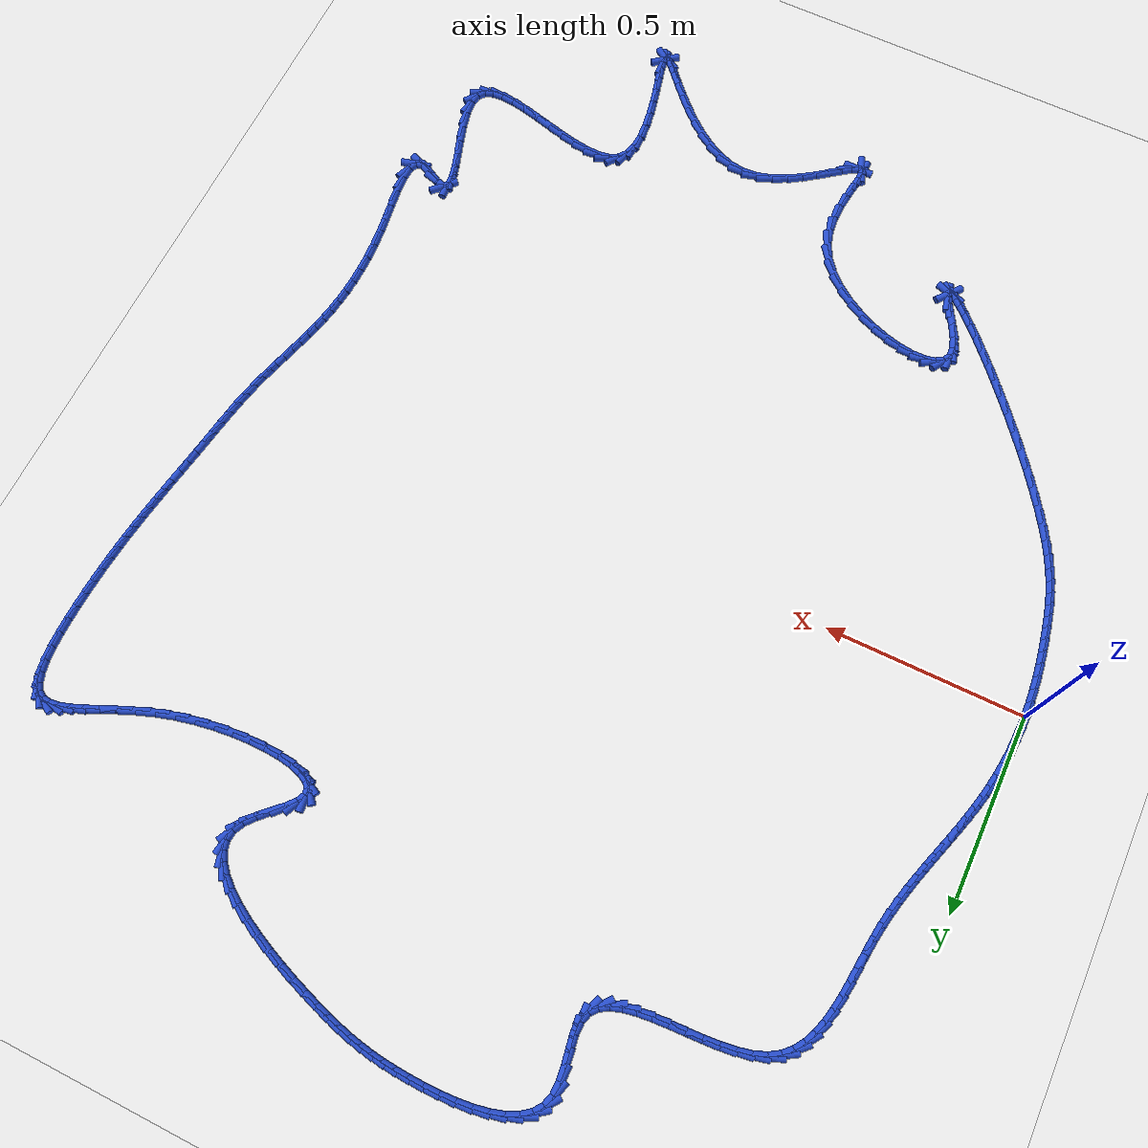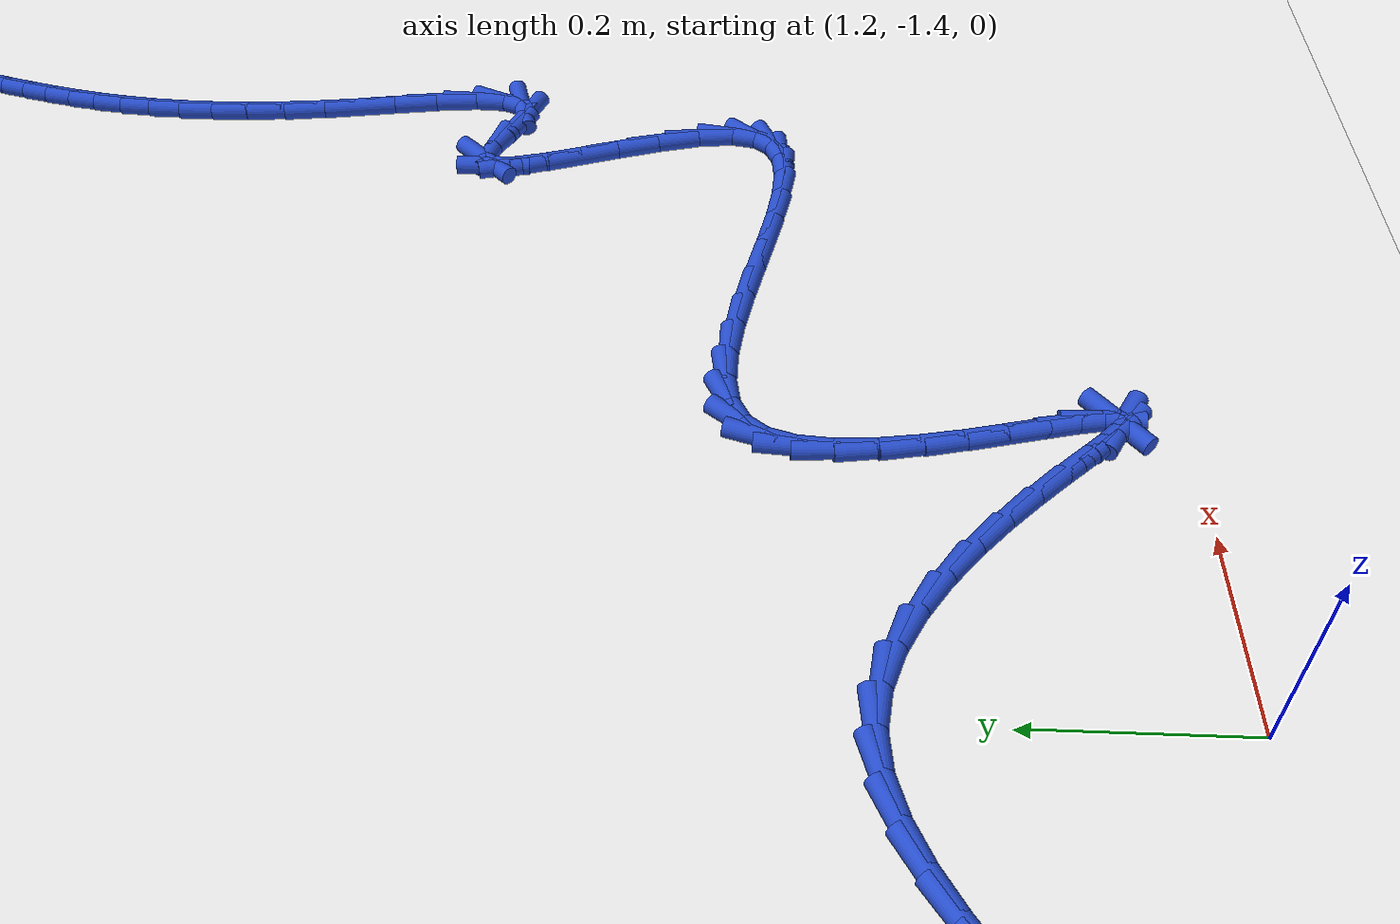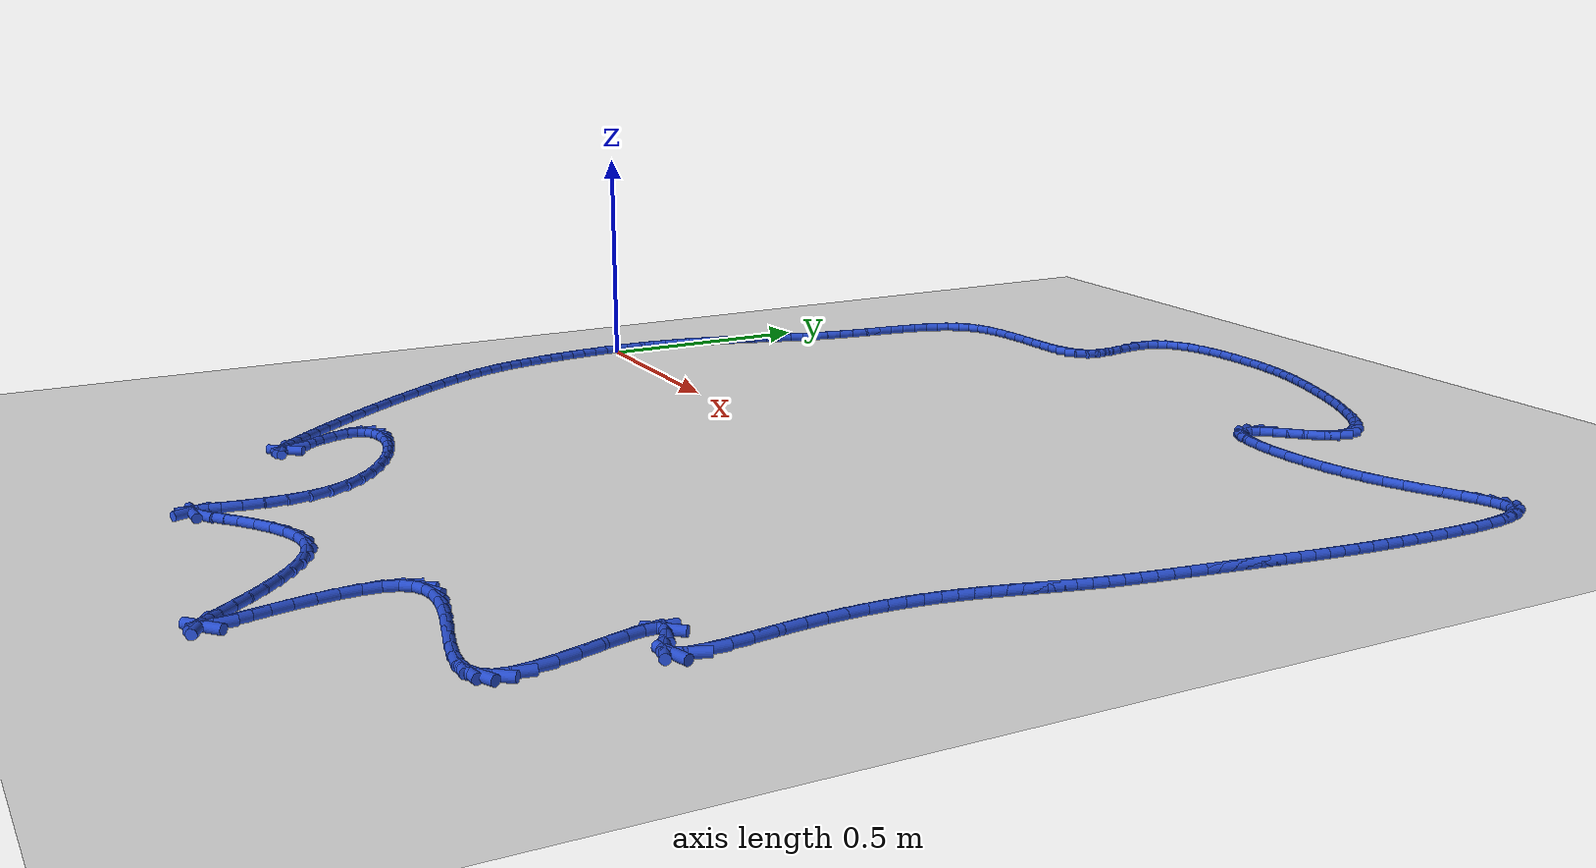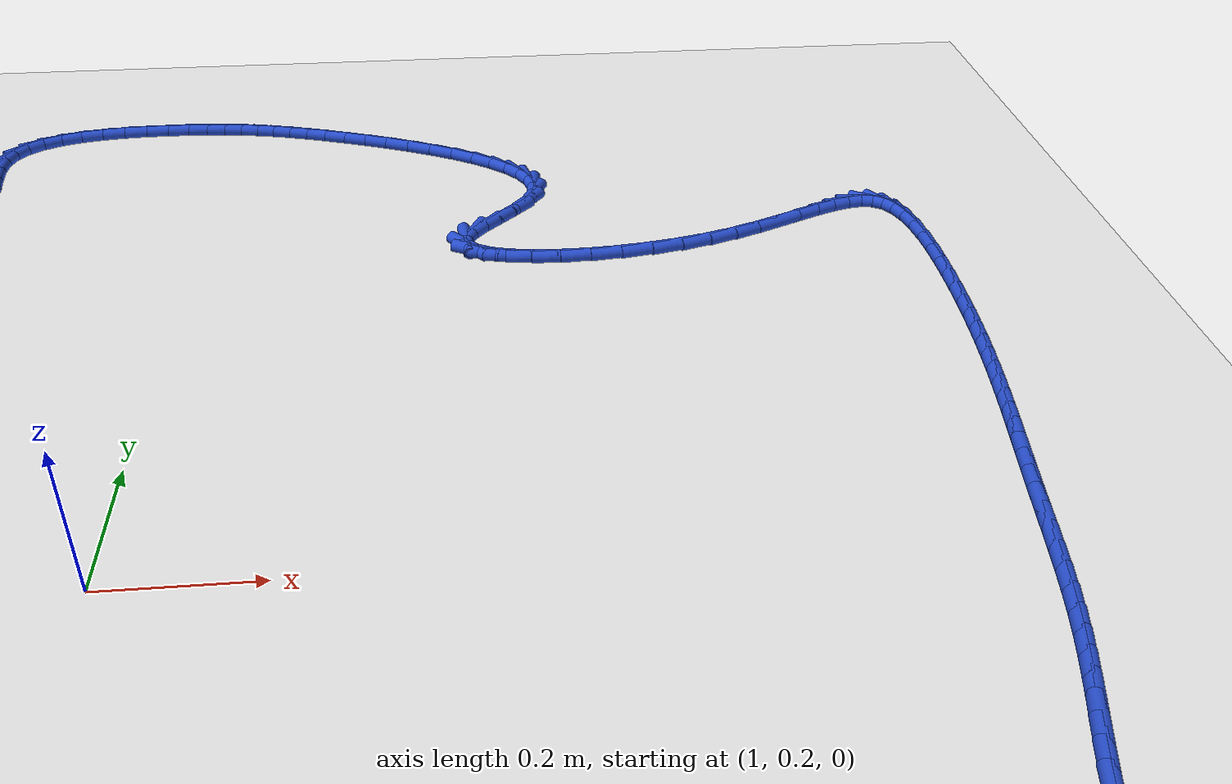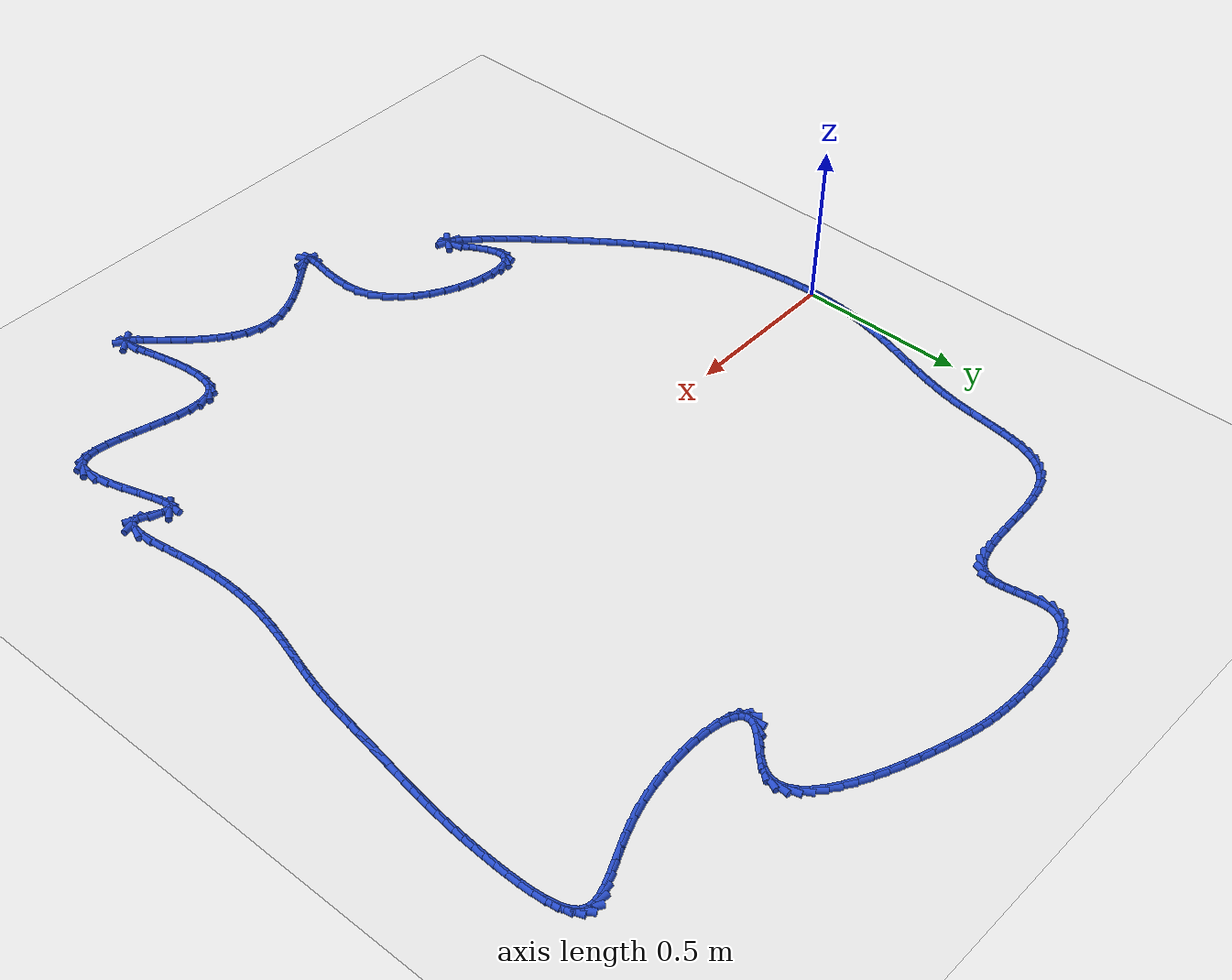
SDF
<sdf version="1.6">
 <world name="default">
  <light name="sun" type="directional">
   <pose>0 0 10 0 -0 0</pose>
   <diffuse>0.8 0.8 0.8 1</diffuse>
   <specular>0.2 0.2 0.2 1</specular>
   <attenuation>
    <range>1000</range>
    <constant>0.9</constant>
    <linear>0.01</linear>
    <quadratic>0.001</quadratic>
   </attenuation>
   <direction>-0.5 0.1 -0.9</direction>
  </light>
  <model name="ground_plane">
   <static>1</static>
   <link name="link">
    <collision name="collision">
     <geometry><plane><normal>0 0 1</normal><size>100 100</size></plane></geometry>
     <surface><friction><ode><mu>100</mu><mu2>50</mu2></ode></friction></surface>
    </collision>
    <visual name="visual">
     <cast_shadows>0</cast_shadows>
     <geometry><plane><normal>0 0 1</normal><size>100 100</size></plane></geometry>
     <material>
      <script><uri>file://media/materials/scripts/gazebo.material</uri><name>Gazebo/WhiteGlow</name></script>
     </material>
    </visual>
   </link>
  </model>
  <gravity>0 0 -9.8</gravity>
  <magnetic_field>6e-06 2.3e-05 -4.2e-05</magnetic_field>
  <atmosphere type="adiabatic"/>
  <physics name="default_physics" default="0" type="ode">
   <max_step_size>0.001</max_step_size>
   <real_time_factor>1</real_time_factor>
   <real_time_update_rate>1000</real_time_update_rate>
  </physics>
  <scene><ambient>0.4 0.4 0.4 1</ambient><background>0.7 0.7 0.7 1</background><shadows>1</shadows></scene>
  <spherical_coordinates>
   <surface_model>EARTH_WGS84</surface_model>
   <latitude_deg>0</latitude_deg>
   <longitude_deg>0</longitude_deg>
   <elevation>0</elevation>
   <heading_deg>0</heading_deg>
  </spherical_coordinates>
  <model name="line">
   <link name="link_0">
    <pose>-7.37257477290143e-18 -5.551115123125783e-17 0.01 0 1.57 1.5632704173522833</pose>
    <collision name="collision">
     <geometry><cylinder><radius>0.01</radius><length>0.08</length></cylinder></geometry>
    </collision>
    <visual name="visual">
     <material>
      <script><name>Gazebo/Blue</name><uri>file://media/materials/scripts/gazebo.material</uri></script>
     </material>
     <geometry><cylinder><radius>0.01</radius><length>0.08</length></cylinder></geometry>
    </visual>
   </link>
   <link name="link_1">
    <pose>0.0002456686995575456 0.03264244185297479 0.01 0 1.57 1.5268009838545717</pose>
    <collision name="collision">
     <geometry><cylinder><radius>0.01</radius><length>0.08</length></cylinder></geometry>
    </collision>
    <visual name="visual">
     <material>
      <script><name>Gazebo/Blue</name><uri>file://media/materials/scripts/gazebo.material</uri></script>
     </material>
     <geometry><cylinder><radius>0.01</radius><length>0.08</length></cylinder></geometry>
    </visual>
   </link>
   <link name="link_2">
    <pose>0.0016749753505119883 0.06510915883912491 0.01 0 1.57 1.4911623278161554</pose>
    <collision name="collision">
     <geometry><cylinder><radius>0.01</radius><length>0.08</length></cylinder></geometry>
    </collision>
    <visual name="visual">
     <material>
      <script><name>Gazebo/Blue</name><uri>file://media/materials/scripts/gazebo.material</uri></script>
     </material>
     <geometry><cylinder><radius>0.01</radius><length>0.08</length></cylinder></geometry>
    </visual>
   </link>
   <link name="link_3">
    <pose>0.00424755348249707 0.09734586426357598 0.01 0 1.57 1.4562697613169648</pose>
    <collision name="collision">
     <geometry><cylinder><radius>0.01</radius><length>0.08</length></cylinder></geometry>
    </collision>
    <visual name="visual">
     <material>
      <script><name>Gazebo/Blue</name><uri>file://media/materials/scripts/gazebo.material</uri></script>
     </material>
     <geometry><cylinder><radius>0.01</radius><length>0.08</length></cylinder></geometry>
    </visual>
   </link>
   <link name="link_4">
    <pose>0.007923036625146547 0.12929827143145375 0.01 0 1.57 1.4220317220771173</pose>
    <collision name="collision">
     <geometry><cylinder><radius>0.01</radius><length>0.08</length></cylinder></geometry>
    </collision>
    <visual name="visual">
     <material>
      <script><name>Gazebo/Blue</name><uri>file://media/materials/scripts/gazebo.material</uri></script>
     </material>
     <geometry><cylinder><radius>0.01</radius><length>0.08</length></cylinder></geometry>
    </visual>
   </link>
   <link name="link_5">
    <pose>0.012661058308094168 0.16091209364788384 0.01 0 1.57 1.3883502762425861</pose>
    <collision name="collision">
     <geometry><cylinder><radius>0.01</radius><length>0.08</length></cylinder></geometry>
    </collision>
    <visual name="visual">
     <material>
      <script><name>Gazebo/Blue</name><uri>file://media/materials/scripts/gazebo.material</uri></script>
     </material>
     <geometry><cylinder><radius>0.01</radius><length>0.08</length></cylinder></geometry>
    </visual>
   </link>
   <link name="link_6">
    <pose>0.018421252060973694 0.19213304421799213 0.01 0 1.57 1.3551213344674293</pose>
    <collision name="collision">
     <geometry><cylinder><radius>0.01</radius><length>0.08</length></cylinder></geometry>
    </collision>
    <visual name="visual">
     <material>
      <script><name>Gazebo/Blue</name><uri>file://media/materials/scripts/gazebo.material</uri></script>
     </material>
     <geometry><cylinder><radius>0.01</radius><length>0.08</length></cylinder></geometry>
    </visual>
   </link>
   <link name="link_7">
    <pose>0.025163251369510278 0.22290683650883564 0.01 0 1.57 1.3231857685717456</pose>
    <collision name="collision">
     <geometry><cylinder><radius>0.01</radius><length>0.08</length></cylinder></geometry>
    </collision>
    <visual name="visual">
     <material>
      <script><name>Gazebo/Blue</name><uri>file://media/materials/scripts/gazebo.material</uri></script>
     </material>
     <geometry><cylinder><radius>0.01</radius><length>0.08</length></cylinder></geometry>
    </visual>
   </link>
   <link name="link_8">
    <pose>0.032824101511070305 0.25321104376012543 0.01 0 1.57 1.2963018387225682</pose>
    <collision name="collision">
     <geometry><cylinder><radius>0.01</radius><length>0.08</length></cylinder></geometry>
    </collision>
    <visual name="visual">
     <material>
      <script><name>Gazebo/Blue</name><uri>file://media/materials/scripts/gazebo.material</uri></script>
     </material>
     <geometry><cylinder><radius>0.01</radius><length>0.08</length></cylinder></geometry>
    </visual>
   </link>
   <link name="link_9">
    <pose>0.041253855787582 0.2831459383303042 0.01 0 1.57 1.2756622982968644</pose>
    <collision name="collision">
     <geometry><cylinder><radius>0.01</radius><length>0.08</length></cylinder></geometry>
    </collision>
    <visual name="visual">
     <material>
      <script><name>Gazebo/Blue</name><uri>file://media/materials/scripts/gazebo.material</uri></script>
     </material>
     <geometry><cylinder><radius>0.01</radius><length>0.08</length></cylinder></geometry>
    </visual>
   </link>
   <link name="link_10">
    <pose>0.05028162869394227 0.31284132602796483 0.01 0 1.57 1.26147710530987</pose>
    <collision name="collision">
     <geometry><cylinder><radius>0.01</radius><length>0.08</length></cylinder></geometry>
    </collision>
    <visual name="visual">
     <material>
      <script><name>Gazebo/Blue</name><uri>file://media/materials/scripts/gazebo.material</uri></script>
     </material>
     <geometry><cylinder><radius>0.01</radius><length>0.08</length></cylinder></geometry>
    </visual>
   </link>
   <link name="link_11">
    <pose>0.05973653472504801 0.3424270126616997 0.01 0 1.57 1.253839580025563</pose>
    <collision name="collision">
     <geometry><cylinder><radius>0.01</radius><length>0.08</length></cylinder></geometry>
    </collision>
    <visual name="visual">
     <material>
      <script><name>Gazebo/Blue</name><uri>file://media/materials/scripts/gazebo.material</uri></script>
     </material>
     <geometry><cylinder><radius>0.01</radius><length>0.08</length></cylinder></geometry>
    </visual>
   </link>
   <link name="link_12">
    <pose>0.06944768837579615 0.3720328040401017 0.01 0 1.57 1.252741911935959</pose>
    <collision name="collision">
     <geometry><cylinder><radius>0.01</radius><length>0.08</length></cylinder></geometry>
    </collision>
    <visual name="visual">
     <material>
      <script><name>Gazebo/Blue</name><uri>file://media/materials/scripts/gazebo.material</uri></script>
     </material>
     <geometry><cylinder><radius>0.01</radius><length>0.08</length></cylinder></geometry>
    </visual>
   </link>
   <link name="link_13">
    <pose>0.07924420414108356 0.40178850597176335 0.01 0 1.57 1.2580864603284783</pose>
    <collision name="collision">
     <geometry><cylinder><radius>0.01</radius><length>0.08</length></cylinder></geometry>
    </collision>
    <visual name="visual">
     <material>
      <script><name>Gazebo/Blue</name><uri>file://media/materials/scripts/gazebo.material</uri></script>
     </material>
     <geometry><cylinder><radius>0.01</radius><length>0.08</length></cylinder></geometry>
    </visual>
   </link>
   <link name="link_14">
    <pose>0.08895519651580716 0.4318239242652773 0.01 0 1.57 1.269691735281175</pose>
    <collision name="collision">
     <geometry><cylinder><radius>0.01</radius><length>0.08</length></cylinder></geometry>
    </collision>
    <visual name="visual">
     <material>
      <script><name>Gazebo/Blue</name><uri>file://media/materials/scripts/gazebo.material</uri></script>
     </material>
     <geometry><cylinder><radius>0.01</radius><length>0.08</length></cylinder></geometry>
    </visual>
   </link>
   <link name="link_15">
    <pose>0.09840977999486385 0.4622688647292362 0.01 0 1.57 1.2872934140344503</pose>
    <collision name="collision">
     <geometry><cylinder><radius>0.01</radius><length>0.08</length></cylinder></geometry>
    </collision>
    <visual name="visual">
     <material>
      <script><name>Gazebo/Blue</name><uri>file://media/materials/scripts/gazebo.material</uri></script>
     </material>
     <geometry><cylinder><radius>0.01</radius><length>0.08</length></cylinder></geometry>
    </visual>
   </link>
   <link name="link_16">
    <pose>0.10743706907315051 0.4932531331722326 0.01 0 1.57 1.3105419493037958</pose>
    <collision name="collision">
     <geometry><cylinder><radius>0.01</radius><length>0.08</length></cylinder></geometry>
    </collision>
    <visual name="visual">
     <material>
      <script><name>Gazebo/Blue</name><uri>file://media/materials/scripts/gazebo.material</uri></script>
     </material>
     <geometry><cylinder><radius>0.01</radius><length>0.08</length></cylinder></geometry>
    </visual>
   </link>
   <link name="link_17">
    <pose>0.11586617824556412 0.5249065354028596 0.01 0 1.57 1.338999227544284</pose>
    <collision name="collision">
     <geometry><cylinder><radius>0.01</radius><length>0.08</length></cylinder></geometry>
    </collision>
    <visual name="visual">
     <material>
      <script><name>Gazebo/Blue</name><uri>file://media/materials/scripts/gazebo.material</uri></script>
     </material>
     <geometry><cylinder><radius>0.01</radius><length>0.08</length></cylinder></geometry>
    </visual>
   </link>
   <link name="link_18">
    <pose>0.12352622200700154 0.5573588772297094 0.01 0 1.57 1.3721372610559748</pose>
    <collision name="collision">
     <geometry><cylinder><radius>0.01</radius><length>0.08</length></cylinder></geometry>
    </collision>
    <visual name="visual">
     <material>
      <script><name>Gazebo/Blue</name><uri>file://media/materials/scripts/gazebo.material</uri></script>
     </material>
     <geometry><cylinder><radius>0.01</radius><length>0.08</length></cylinder></geometry>
    </visual>
   </link>
   <link name="link_19">
    <pose>0.1302463148523597 0.590739964461375 0.01 0 1.57 1.4093081269379566</pose>
    <collision name="collision">
     <geometry><cylinder><radius>0.01</radius><length>0.08</length></cylinder></geometry>
    </collision>
    <visual name="visual">
     <material>
      <script><name>Gazebo/Blue</name><uri>file://media/materials/scripts/gazebo.material</uri></script>
     </material>
     <geometry><cylinder><radius>0.01</radius><length>0.08</length></cylinder></geometry>
    </visual>
   </link>
   <link name="link_20">
    <pose>0.1358566157395685 0.6251786825634659 0.01 0 1.57 1.4431699990393103</pose>
    <collision name="collision">
     <geometry><cylinder><radius>0.01</radius><length>0.08</length></cylinder></geometry>
    </collision>
    <visual name="visual">
     <material>
      <script><name>Gazebo/Blue</name><uri>file://media/materials/scripts/gazebo.material</uri></script>
     </material>
     <geometry><cylinder><radius>0.01</radius><length>0.08</length></cylinder></geometry>
    </visual>
   </link>
   <link name="link_21">
    <pose>0.14040370964791052 0.6606132102329533 0.01 0 1.57 1.4596717704684488</pose>
    <collision name="collision">
     <geometry><cylinder><radius>0.01</radius><length>0.08</length></cylinder></geometry>
    </collision>
    <visual name="visual">
     <material>
      <script><name>Gazebo/Blue</name><uri>file://media/materials/scripts/gazebo.material</uri></script>
     </material>
     <geometry><cylinder><radius>0.01</radius><length>0.08</length></cylinder></geometry>
    </visual>
   </link>
   <link name="link_22">
    <pose>0.1444146238691144 0.6965583778080858 0.01 0 1.57 1.458049661329926</pose>
    <collision name="collision">
     <geometry><cylinder><radius>0.01</radius><length>0.08</length></cylinder></geometry>
    </collision>
    <visual name="visual">
     <material>
      <script><name>Gazebo/Blue</name><uri>file://media/materials/scripts/gazebo.material</uri></script>
     </material>
     <geometry><cylinder><radius>0.01</radius><length>0.08</length></cylinder></geometry>
    </visual>
   </link>
   <link name="link_23">
    <pose>0.14848101732431127 0.7324720645769656 0.01 0 1.57 1.4382025285937923</pose>
    <collision name="collision">
     <geometry><cylinder><radius>0.01</radius><length>0.08</length></cylinder></geometry>
    </collision>
    <visual name="visual">
     <material>
      <script><name>Gazebo/Blue</name><uri>file://media/materials/scripts/gazebo.material</uri></script>
     </material>
     <geometry><cylinder><radius>0.01</radius><length>0.08</length></cylinder></geometry>
    </visual>
   </link>
   <link name="link_24">
    <pose>0.15319454893463189 0.7678121498276936 0.01 0 1.57 1.398597980906987</pose>
    <collision name="collision">
     <geometry><cylinder><radius>0.01</radius><length>0.08</length></cylinder></geometry>
    </collision>
    <visual name="visual">
     <material>
      <script><name>Gazebo/Blue</name><uri>file://media/materials/scripts/gazebo.material</uri></script>
     </material>
     <geometry><cylinder><radius>0.01</radius><length>0.08</length></cylinder></geometry>
    </visual>
   </link>
   <link name="link_25">
    <pose>0.15914687762120733 0.8020365128483721 0.01 0 1.57 1.336214921331327</pose>
    <collision name="collision">
     <geometry><cylinder><radius>0.01</radius><length>0.08</length></cylinder></geometry>
    </collision>
    <visual name="visual">
     <material>
      <script><name>Gazebo/Blue</name><uri>file://media/materials/scripts/gazebo.material</uri></script>
     </material>
     <geometry><cylinder><radius>0.01</radius><length>0.08</length></cylinder></geometry>
    </visual>
   </link>
   <link name="link_26">
    <pose>0.16692966230516856 0.8346030329271025 0.01 0 1.57 1.246596308479444</pose>
    <collision name="collision">
     <geometry><cylinder><radius>0.01</radius><length>0.08</length></cylinder></geometry>
    </collision>
    <visual name="visual">
     <material>
      <script><name>Gazebo/Blue</name><uri>file://media/materials/scripts/gazebo.material</uri></script>
     </material>
     <geometry><cylinder><radius>0.01</radius><length>0.08</length></cylinder></geometry>
    </visual>
   </link>
   <link name="link_27">
    <pose>0.1771345619076465 0.8649695893519866 0.01 0 1.57 1.1244854717149042</pose>
    <collision name="collision">
     <geometry><cylinder><radius>0.01</radius><length>0.08</length></cylinder></geometry>
    </collision>
    <visual name="visual">
     <material>
      <script><name>Gazebo/Blue</name><uri>file://media/materials/scripts/gazebo.material</uri></script>
     </material>
     <geometry><cylinder><radius>0.01</radius><length>0.08</length></cylinder></geometry>
    </visual>
   </link>
   <link name="link_28">
    <pose>0.19035323534977217 0.8925940614111261 0.01 0 1.57 0.9659976913463877</pose>
    <collision name="collision">
     <geometry><cylinder><radius>0.01</radius><length>0.08</length></cylinder></geometry>
    </collision>
    <visual name="visual">
     <material>
      <script><name>Gazebo/Blue</name><uri>file://media/materials/scripts/gazebo.material</uri></script>
     </material>
     <geometry><cylinder><radius>0.01</radius><length>0.08</length></cylinder></geometry>
    </visual>
   </link>
   <link name="link_29">
    <pose>0.20717734155267659 0.9169343283926229 0.01 0 1.57 0.7731860584852928</pose>
    <collision name="collision">
     <geometry><cylinder><radius>0.01</radius><length>0.08</length></cylinder></geometry>
    </collision>
    <visual name="visual">
     <material>
      <script><name>Gazebo/Blue</name><uri>file://media/materials/scripts/gazebo.material</uri></script>
     </material>
     <geometry><cylinder><radius>0.01</radius><length>0.08</length></cylinder></geometry>
    </visual>
   </link>
   <link name="link_30">
    <pose>0.22819853943749063 0.9374482695845785 0.01 0 1.57 0.5593678392755799</pose>
    <collision name="collision">
     <geometry><cylinder><radius>0.01</radius><length>0.08</length></cylinder></geometry>
    </collision>
    <visual name="visual">
     <material>
      <script><name>Gazebo/Blue</name><uri>file://media/materials/scripts/gazebo.material</uri></script>
     </material>
     <geometry><cylinder><radius>0.01</radius><length>0.08</length></cylinder></geometry>
    </visual>
   </link>
   <link name="link_31">
    <pose>0.25399944191988844 0.9536014210547102 0.01 0 1.57 0.3672177687692208</pose>
    <collision name="collision">
     <geometry><cylinder><radius>0.01</radius><length>0.08</length></cylinder></geometry>
    </collision>
    <visual name="visual">
     <material>
      <script><name>Gazebo/Blue</name><uri>file://media/materials/scripts/gazebo.material</uri></script>
     </material>
     <geometry><cylinder><radius>0.01</radius><length>0.08</length></cylinder></geometry>
    </visual>
   </link>
   <link name="link_32">
    <pose>0.2845700762271755 0.9653608991584091 0.01 0 1.57 0.2323511931777744</pose>
    <collision name="collision">
     <geometry><cylinder><radius>0.01</radius><length>0.08</length></cylinder></geometry>
    </collision>
    <visual name="visual">
     <material>
      <script><name>Gazebo/Blue</name><uri>file://media/materials/scripts/gazebo.material</uri></script>
     </material>
     <geometry><cylinder><radius>0.01</radius><length>0.08</length></cylinder></geometry>
    </visual>
   </link>
   <link name="link_33">
    <pose>0.31895210548877895 0.9734965408472075 0.01 0 1.57 0.14312621092465375</pose>
    <collision name="collision">
     <geometry><cylinder><radius>0.01</radius><length>0.08</length></cylinder></geometry>
    </collision>
    <visual name="visual">
     <material>
      <script><name>Gazebo/Blue</name><uri>file://media/materials/scripts/gazebo.material</uri></script>
     </material>
     <geometry><cylinder><radius>0.01</radius><length>0.08</length></cylinder></geometry>
    </visual>
   </link>
   <link name="link_34">
    <pose>0.35610202098449195 0.97885027479149 0.01 0 1.57 0.08759053638613644</pose>
    <collision name="collision">
     <geometry><cylinder><radius>0.01</radius><length>0.08</length></cylinder></geometry>
    </collision>
    <visual name="visual">
     <material>
      <script><name>Gazebo/Blue</name><uri>file://media/materials/scripts/gazebo.material</uri></script>
     </material>
     <geometry><cylinder><radius>0.01</radius><length>0.08</length></cylinder></geometry>
    </visual>
   </link>
   <link name="link_35">
    <pose>0.3949763139941072 0.9822640296616401 0.01 0 1.57 0.058476926967701306</pose>
    <collision name="collision">
     <geometry><cylinder><radius>0.01</radius><length>0.08</length></cylinder></geometry>
    </collision>
    <visual name="visual">
     <material>
      <script><name>Gazebo/Blue</name><uri>file://media/materials/scripts/gazebo.material</uri></script>
     </material>
     <geometry><cylinder><radius>0.01</radius><length>0.08</length></cylinder></geometry>
    </visual>
   </link>
   <link name="link_36">
    <pose>0.43453147579741785 0.9845797341280421 0.01 0 1.57 0.052502107369102845</pose>
    <collision name="collision">
     <geometry><cylinder><radius>0.01</radius><length>0.08</length></cylinder></geometry>
    </collision>
    <visual name="visual">
     <material>
      <script><name>Gazebo/Blue</name><uri>file://media/materials/scripts/gazebo.material</uri></script>
     </material>
     <geometry><cylinder><radius>0.01</radius><length>0.08</length></cylinder></geometry>
    </visual>
   </link>
   <link name="link_37">
    <pose>0.47372399767421725 0.9866393168610799 0.01 0 1.57 0.06989504903849242</pose>
    <collision name="collision">
     <geometry><cylinder><radius>0.01</radius><length>0.08</length></cylinder></geometry>
    </collision>
    <visual name="visual">
     <material>
      <script><name>Gazebo/Blue</name><uri>file://media/materials/scripts/gazebo.material</uri></script>
     </material>
     <geometry><cylinder><radius>0.01</radius><length>0.08</length></cylinder></geometry>
    </visual>
   </link>
   <link name="link_38">
    <pose>0.5115103709042979 0.9892847065311378 0.01 0 1.57 0.11475964148842825</pose>
    <collision name="collision">
     <geometry><cylinder><radius>0.01</radius><length>0.08</length></cylinder></geometry>
    </collision>
    <visual name="visual">
     <material>
      <script><name>Gazebo/Blue</name><uri>file://media/materials/scripts/gazebo.material</uri></script>
     </material>
     <geometry><cylinder><radius>0.01</radius><length>0.08</length></cylinder></geometry>
    </visual>
   </link>
   <link name="link_39">
    <pose>0.5468470867674531 0.9933578318085992 0.01 0 1.57 0.19661275269953515</pose>
    <collision name="collision">
     <geometry><cylinder><radius>0.01</radius><length>0.08</length></cylinder></geometry>
    </collision>
    <visual name="visual">
     <material>
      <script><name>Gazebo/Blue</name><uri>file://media/materials/scripts/gazebo.material</uri></script>
     </material>
     <geometry><cylinder><radius>0.01</radius><length>0.08</length></cylinder></geometry>
    </visual>
   </link>
   <link name="link_40">
    <pose>0.5786906365434755 0.9997006213638486 0.01 0 1.57 0.33330979281576223</pose>
    <collision name="collision">
     <geometry><cylinder><radius>0.01</radius><length>0.08</length></cylinder></geometry>
    </collision>
    <visual name="visual">
     <material>
      <script><name>Gazebo/Blue</name><uri>file://media/materials/scripts/gazebo.material</uri></script>
     </material>
     <geometry><cylinder><radius>0.01</radius><length>0.08</length></cylinder></geometry>
    </visual>
   </link>
   <link name="link_41">
    <pose>0.6059975115121591 1.0091550038672705 0.01 0 1.57 0.5529103301493403</pose>
    <collision name="collision">
     <geometry><cylinder><radius>0.01</radius><length>0.08</length></cylinder></geometry>
    </collision>
    <visual name="visual">
     <material>
      <script><name>Gazebo/Blue</name><uri>file://media/materials/scripts/gazebo.material</uri></script>
     </material>
     <geometry><cylinder><radius>0.01</radius><length>0.08</length></cylinder></geometry>
    </visual>
   </link>
   <link name="link_42">
    <pose>0.6277242029532957 1.0225629079892478 0.01 0 1.57 0.878216688704699</pose>
    <collision name="collision">
     <geometry><cylinder><radius>0.01</radius><length>0.08</length></cylinder></geometry>
    </collision>
    <visual name="visual">
     <material>
      <script><name>Gazebo/Blue</name><uri>file://media/materials/scripts/gazebo.material</uri></script>
     </material>
     <geometry><cylinder><radius>0.01</radius><length>0.08</length></cylinder></geometry>
    </visual>
   </link>
   <link name="link_43">
    <pose>0.6428272021466788 1.0407662624001652 0.01 0 1.57 1.2678326695225448</pose>
    <collision name="collision">
     <geometry><cylinder><radius>0.01</radius><length>0.08</length></cylinder></geometry>
    </collision>
    <visual name="visual">
     <material>
      <script><name>Gazebo/Blue</name><uri>file://media/materials/scripts/gazebo.material</uri></script>
     </material>
     <geometry><cylinder><radius>0.01</radius><length>0.08</length></cylinder></geometry>
    </visual>
   </link>
   <link name="link_44">
    <pose>0.6502765298399066 1.0645975156520313 0.01 0 1.57 1.5665873825607752</pose>
    <collision name="collision">
     <geometry><cylinder><radius>0.01</radius><length>0.08</length></cylinder></geometry>
    </collision>
    <visual name="visual">
     <material>
      <script><name>Gazebo/Blue</name><uri>file://media/materials/scripts/gazebo.material</uri></script>
     </material>
     <geometry><cylinder><radius>0.01</radius><length>0.08</length></cylinder></geometry>
    </visual>
   </link>
   <link name="link_45">
    <pose>0.6504000217407532 1.0939376933184923 0.01 0 1.57 -1.4388866192588754</pose>
    <collision name="collision">
     <geometry><cylinder><radius>0.01</radius><length>0.08</length></cylinder></geometry>
    </collision>
    <visual name="visual">
     <material>
      <script><name>Gazebo/Blue</name><uri>file://media/materials/scripts/gazebo.material</uri></script>
     </material>
     <geometry><cylinder><radius>0.01</radius><length>0.08</length></cylinder></geometry>
    </visual>
   </link>
   <link name="link_46">
    <pose>0.6460243365846805 1.1269168919312207 0.01 0 1.57 -1.4050988027880247</pose>
    <collision name="collision">
     <geometry><cylinder><radius>0.01</radius><length>0.08</length></cylinder></geometry>
    </collision>
    <visual name="visual">
     <material>
      <script><name>Gazebo/Blue</name><uri>file://media/materials/scripts/gazebo.material</uri></script>
     </material>
     <geometry><cylinder><radius>0.01</radius><length>0.08</length></cylinder></geometry>
    </visual>
   </link>
   <link name="link_47">
    <pose>0.6402448335303893 1.1614769292324616 0.01 0 1.57 -1.451424134062492</pose>
    <collision name="collision">
     <geometry><cylinder><radius>0.01</radius><length>0.08</length></cylinder></geometry>
    </collision>
    <visual name="visual">
     <material>
      <script><name>Gazebo/Blue</name><uri>file://media/materials/scripts/gazebo.material</uri></script>
     </material>
     <geometry><cylinder><radius>0.01</radius><length>0.08</length></cylinder></geometry>
    </visual>
   </link>
   <link name="link_48">
    <pose>0.6361568717365808 1.1955596229644632 0.01 0 1.57 1.5486445982817794</pose>
    <collision name="collision">
     <geometry><cylinder><radius>0.01</radius><length>0.08</length></cylinder></geometry>
    </collision>
    <visual name="visual">
     <material>
      <script><name>Gazebo/Blue</name><uri>file://media/materials/scripts/gazebo.material</uri></script>
     </material>
     <geometry><cylinder><radius>0.01</radius><length>0.08</length></cylinder></geometry>
    </visual>
   </link>
   <link name="link_49">
    <pose>0.6368558103619562 1.22710679086947 0.01 0 1.57 1.2722423378001668</pose>
    <collision name="collision">
     <geometry><cylinder><radius>0.01</radius><length>0.08</length></cylinder></geometry>
    </collision>
    <visual name="visual">
     <material>
      <script><name>Gazebo/Blue</name><uri>file://media/materials/scripts/gazebo.material</uri></script>
     </material>
     <geometry><cylinder><radius>0.01</radius><length>0.08</length></cylinder></geometry>
    </visual>
   </link>
   <link name="link_50">
    <pose>0.6451943814043819 1.2542018393619834 0.01 0 1.57 0.9376428209108588</pose>
    <collision name="collision">
     <geometry><cylinder><radius>0.01</radius><length>0.08</length></cylinder></geometry>
    </collision>
    <visual name="visual">
     <material>
      <script><name>Gazebo/Blue</name><uri>file://media/materials/scripts/gazebo.material</uri></script>
     </material>
     <geometry><cylinder><radius>0.01</radius><length>0.08</length></cylinder></geometry>
    </visual>
   </link>
   <link name="link_51">
    <pose>0.6614917498632273 1.2764066753926713 0.01 0 1.57 0.6560295995454712</pose>
    <collision name="collision">
     <geometry><cylinder><radius>0.01</radius><length>0.08</length></cylinder></geometry>
    </collision>
    <visual name="visual">
     <material>
      <script><name>Gazebo/Blue</name><uri>file://media/materials/scripts/gazebo.material</uri></script>
     </material>
     <geometry><cylinder><radius>0.01</radius><length>0.08</length></cylinder></geometry>
    </visual>
   </link>
   <link name="link_52">
    <pose>0.6845592137779092 1.294163144003472 0.01 0 1.57 0.44808116099991324</pose>
    <collision name="collision">
     <geometry><cylinder><radius>0.01</radius><length>0.08</length></cylinder></geometry>
    </collision>
    <visual name="visual">
     <material>
      <script><name>Gazebo/Blue</name><uri>file://media/materials/scripts/gazebo.material</uri></script>
     </material>
     <geometry><cylinder><radius>0.01</radius><length>0.08</length></cylinder></geometry>
    </visual>
   </link>
   <link name="link_53">
    <pose>0.7131880645191384 1.3079247654240826 0.01 0 1.57 0.30049558620867545</pose>
    <collision name="collision">
     <geometry><cylinder><radius>0.01</radius><length>0.08</length></cylinder></geometry>
    </collision>
    <visual name="visual">
     <material>
      <script><name>Gazebo/Blue</name><uri>file://media/materials/scripts/gazebo.material</uri></script>
     </material>
     <geometry><cylinder><radius>0.01</radius><length>0.08</length></cylinder></geometry>
    </visual>
   </link>
   <link name="link_54">
    <pose>0.746169593457626 1.3181450598841995 0.01 0 1.57 0.194929331847569</pose>
    <collision name="collision">
     <geometry><cylinder><radius>0.01</radius><length>0.08</length></cylinder></geometry>
    </collision>
    <visual name="visual">
     <material>
      <script><name>Gazebo/Blue</name><uri>file://media/materials/scripts/gazebo.material</uri></script>
     </material>
     <geometry><cylinder><radius>0.01</radius><length>0.08</length></cylinder></geometry>
    </visual>
   </link>
   <link name="link_55">
    <pose>0.7822950919640842 1.3252775476135201 0.01 0 1.57 0.11763905921892041</pose>
    <collision name="collision">
     <geometry><cylinder><radius>0.01</radius><length>0.08</length></cylinder></geometry>
    </collision>
    <visual name="visual">
     <material>
      <script><name>Gazebo/Blue</name><uri>file://media/materials/scripts/gazebo.material</uri></script>
     </material>
     <geometry><cylinder><radius>0.01</radius><length>0.08</length></cylinder></geometry>
    </visual>
   </link>
   <link name="link_56">
    <pose>0.8203558514092228 1.3297757488417417 0.01 0 1.57 0.05967630139571058</pose>
    <collision name="collision">
     <geometry><cylinder><radius>0.01</radius><length>0.08</length></cylinder></geometry>
    </collision>
    <visual name="visual">
     <material>
      <script><name>Gazebo/Blue</name><uri>file://media/materials/scripts/gazebo.material</uri></script>
     </material>
     <geometry><cylinder><radius>0.01</radius><length>0.08</length></cylinder></geometry>
    </visual>
   </link>
   <link name="link_57">
    <pose>0.8591431631637547 1.3320931837985612 0.01 0 1.57 0.015406339247521123</pose>
    <collision name="collision">
     <geometry><cylinder><radius>0.01</radius><length>0.08</length></cylinder></geometry>
    </collision>
    <visual name="visual">
     <material>
      <script><name>Gazebo/Blue</name><uri>file://media/materials/scripts/gazebo.material</uri></script>
     </material>
     <geometry><cylinder><radius>0.01</radius><length>0.08</length></cylinder></geometry>
    </visual>
   </link>
   <link name="link_58">
    <pose>0.8974483185983897 1.3326833727136753 0.01 0 1.57 -0.01866668871540023</pose>
    <collision name="collision">
     <geometry><cylinder><radius>0.01</radius><length>0.08</length></cylinder></geometry>
    </collision>
    <visual name="visual">
     <material>
      <script><name>Gazebo/Blue</name><uri>file://media/materials/scripts/gazebo.material</uri></script>
     </material>
     <geometry><cylinder><radius>0.01</radius><length>0.08</length></cylinder></geometry>
    </visual>
   </link>
   <link name="link_59">
    <pose>0.9340626460760861 1.3319998250653 0.01 0 1.57 -0.04717963091116481</pose>
    <collision name="collision">
     <geometry><cylinder><radius>0.01</radius><length>0.08</length></cylinder></geometry>
    </collision>
    <visual name="visual">
     <material>
      <script><name>Gazebo/Blue</name><uri>file://media/materials/scripts/gazebo.material</uri></script>
     </material>
     <geometry><cylinder><radius>0.01</radius><length>0.08</length></cylinder></geometry>
    </visual>
   </link>
   <link name="link_60">
    <pose>0.9681392240594682 1.330390910745923 0.01 0 1.57 -0.07963552685895688</pose>
    <collision name="collision">
     <geometry><cylinder><radius>0.01</radius><length>0.08</length></cylinder></geometry>
    </collision>
    <visual name="visual">
     <material>
      <script><name>Gazebo/Blue</name><uri>file://media/materials/scripts/gazebo.material</uri></script>
     </material>
     <geometry><cylinder><radius>0.01</radius><length>0.08</length></cylinder></geometry>
    </visual>
   </link>
   <link name="link_61">
    <pose>1.000080602457379 1.3278418514129569 0.01 0 1.57 -0.1170002863810487</pose>
    <collision name="collision">
     <geometry><cylinder><radius>0.01</radius><length>0.08</length></cylinder></geometry>
    </collision>
    <visual name="visual">
     <material>
      <script><name>Gazebo/Blue</name><uri>file://media/materials/scripts/gazebo.material</uri></script>
     </material>
     <geometry><cylinder><radius>0.01</radius><length>0.08</length></cylinder></geometry>
    </visual>
   </link>
   <link name="link_62">
    <pose>1.030558900934862 1.324259520569885 0.01 0 1.57 -0.15730032641291075</pose>
    <collision name="collision">
     <geometry><cylinder><radius>0.01</radius><length>0.08</length></cylinder></geometry>
    </collision>
    <visual name="visual">
     <material>
      <script><name>Gazebo/Blue</name><uri>file://media/materials/scripts/gazebo.material</uri></script>
     </material>
     <geometry><cylinder><radius>0.01</radius><length>0.08</length></cylinder></geometry>
    </visual>
   </link>
   <link name="link_63">
    <pose>1.0602462391569634 1.3195507917201923 0.01 0 1.57 -0.19786879114366193</pose>
    <collision name="collision">
     <geometry><cylinder><radius>0.01</radius><length>0.08</length></cylinder></geometry>
    </collision>
    <visual name="visual">
     <material>
      <script><name>Gazebo/Blue</name><uri>file://media/materials/scripts/gazebo.material</uri></script>
     </material>
     <geometry><cylinder><radius>0.01</radius><length>0.08</length></cylinder></geometry>
    </visual>
   </link>
   <link name="link_64">
    <pose>1.0898147367887265 1.313622538367363 0.01 0 1.57 -0.2359115247043446</pose>
    <collision name="collision">
     <geometry><cylinder><radius>0.01</radius><length>0.08</length></cylinder></geometry>
    </collision>
    <visual name="visual">
     <material>
      <script><name>Gazebo/Blue</name><uri>file://media/materials/scripts/gazebo.material</uri></script>
     </material>
     <geometry><cylinder><radius>0.01</radius><length>0.08</length></cylinder></geometry>
    </visual>
   </link>
   <link name="link_65">
    <pose>1.1199365134951969 1.3063816340148815 0.01 0 1.57 -0.26914333723932476</pose>
    <collision name="collision">
     <geometry><cylinder><radius>0.01</radius><length>0.08</length></cylinder></geometry>
    </collision>
    <visual name="visual">
     <material>
      <script><name>Gazebo/Blue</name><uri>file://media/materials/scripts/gazebo.material</uri></script>
     </material>
     <geometry><cylinder><radius>0.01</radius><length>0.08</length></cylinder></geometry>
    </visual>
   </link>
   <link name="link_66">
    <pose>1.15128368894142 1.2977349521662322 0.01 0 1.57 -0.2962014660045895</pose>
    <collision name="collision">
     <geometry><cylinder><radius>0.01</radius><length>0.08</length></cylinder></geometry>
    </collision>
    <visual name="visual">
     <material>
      <script><name>Gazebo/Blue</name><uri>file://media/materials/scripts/gazebo.material</uri></script>
     </material>
     <geometry><cylinder><radius>0.01</radius><length>0.08</length></cylinder></geometry>
    </visual>
   </link>
   <link name="link_67">
    <pose>1.1845283827924395 1.2875893663248998 0.01 0 1.57 -0.31699612338359107</pose>
    <collision name="collision">
     <geometry><cylinder><radius>0.01</radius><length>0.08</length></cylinder></geometry>
    </collision>
    <visual name="visual">
     <material>
      <script><name>Gazebo/Blue</name><uri>file://media/materials/scripts/gazebo.material</uri></script>
     </material>
     <geometry><cylinder><radius>0.01</radius><length>0.08</length></cylinder></geometry>
    </visual>
   </link>
   <link name="link_68">
    <pose>1.2202897062401392 1.2758575440553679 0.01 0 1.57 -0.33672678658293276</pose>
    <collision name="collision">
     <geometry><cylinder><radius>0.01</radius><length>0.08</length></cylinder></geometry>
    </collision>
    <visual name="visual">
     <material>
      <script><name>Gazebo/Blue</name><uri>file://media/materials/scripts/gazebo.material</uri></script>
     </material>
     <geometry><cylinder><radius>0.01</radius><length>0.08</length></cylinder></geometry>
    </visual>
   </link>
   <link name="link_69">
    <pose>1.2583109783198574 1.2625478808855013 0.01 0 1.57 -0.3601299603547859</pose>
    <collision name="collision">
     <geometry><cylinder><radius>0.01</radius><length>0.08</length></cylinder></geometry>
    </collision>
    <visual name="visual">
     <material>
      <script><name>Gazebo/Blue</name><uri>file://media/materials/scripts/gazebo.material</uri></script>
     </material>
     <geometry><cylinder><radius>0.01</radius><length>0.08</length></cylinder></geometry>
    </visual>
   </link>
   <link name="link_70">
    <pose>1.2976164029795207 1.247747374808648 0.01 0 1.57 -0.3884289713091154</pose>
    <collision name="collision">
     <geometry><cylinder><radius>0.01</radius><length>0.08</length></cylinder></geometry>
    </collision>
    <visual name="visual">
     <material>
      <script><name>Gazebo/Blue</name><uri>file://media/materials/scripts/gazebo.material</uri></script>
     </material>
     <geometry><cylinder><radius>0.01</radius><length>0.08</length></cylinder></geometry>
    </visual>
   </link>
   <link name="link_71">
    <pose>1.3372088932361523 1.2315453510112444 0.01 0 1.57 -0.42321970724465235</pose>
    <collision name="collision">
     <geometry><cylinder><radius>0.01</radius><length>0.08</length></cylinder></geometry>
    </collision>
    <visual name="visual">
     <material>
      <script><name>Gazebo/Blue</name><uri>file://media/materials/scripts/gazebo.material</uri></script>
     </material>
     <geometry><cylinder><radius>0.01</radius><length>0.08</length></cylinder></geometry>
    </visual>
   </link>
   <link name="link_72">
    <pose>1.3760913621067756 1.2140311346797272 0.01 0 1.57 -0.46685754430328025</pose>
    <collision name="collision">
     <geometry><cylinder><radius>0.01</radius><length>0.08</length></cylinder></geometry>
    </collision>
    <visual name="visual">
     <material>
      <script><name>Gazebo/Blue</name><uri>file://media/materials/scripts/gazebo.material</uri></script>
     </material>
     <geometry><cylinder><radius>0.01</radius><length>0.08</length></cylinder></geometry>
    </visual>
   </link>
   <link name="link_73">
    <pose>1.4132667226084132 1.1952940510005328 0.01 0 1.57 -0.5229172722453892</pose>
    <collision name="collision">
     <geometry><cylinder><radius>0.01</radius><length>0.08</length></cylinder></geometry>
    </collision>
    <visual name="visual">
     <material>
      <script><name>Gazebo/Blue</name><uri>file://media/materials/scripts/gazebo.material</uri></script>
     </material>
     <geometry><cylinder><radius>0.01</radius><length>0.08</length></cylinder></geometry>
    </visual>
   </link>
   <link name="link_74">
    <pose>1.4477378877580875 1.1754234251600972 0.01 0 1.57 -0.5969837903980968</pose>
    <collision name="collision">
     <geometry><cylinder><radius>0.01</radius><length>0.08</length></cylinder></geometry>
    </collision>
    <visual name="visual">
     <material>
      <script><name>Gazebo/Blue</name><uri>file://media/materials/scripts/gazebo.material</uri></script>
     </material>
     <geometry><cylinder><radius>0.01</radius><length>0.08</length></cylinder></geometry>
    </visual>
   </link>
   <link name="link_75">
    <pose>1.4785077705728222 1.1545085823448573 0.01 0 1.57 -0.6979772121660366</pose>
    <collision name="collision">
     <geometry><cylinder><radius>0.01</radius><length>0.08</length></cylinder></geometry>
    </collision>
    <visual name="visual">
     <material>
      <script><name>Gazebo/Blue</name><uri>file://media/materials/scripts/gazebo.material</uri></script>
     </material>
     <geometry><cylinder><radius>0.01</radius><length>0.08</length></cylinder></geometry>
    </visual>
   </link>
   <link name="link_76">
    <pose>1.5045792840696408 1.13263884774125 0.01 0 1.57 -0.8400680507557571</pose>
    <collision name="collision">
     <geometry><cylinder><radius>0.01</radius><length>0.08</length></cylinder></geometry>
    </collision>
    <visual name="visual">
     <material>
      <script><name>Gazebo/Blue</name><uri>file://media/materials/scripts/gazebo.material</uri></script>
     </material>
     <geometry><cylinder><radius>0.01</radius><length>0.08</length></cylinder></geometry>
    </visual>
   </link>
   <link name="link_77">
    <pose>1.5249553412655652 1.1099035465357106 0.01 0 1.57 -1.0437237522075464</pose>
    <collision name="collision">
     <geometry><cylinder><radius>0.01</radius><length>0.08</length></cylinder></geometry>
    </collision>
    <visual name="visual">
     <material>
      <script><name>Gazebo/Blue</name><uri>file://media/materials/scripts/gazebo.material</uri></script>
     </material>
     <geometry><cylinder><radius>0.01</radius><length>0.08</length></cylinder></geometry>
    </visual>
   </link>
   <link name="link_78">
    <pose>1.53863885517762 1.086392003914676 0.01 0 1.57 -1.327986443380439</pose>
    <collision name="collision">
     <geometry><cylinder><radius>0.01</radius><length>0.08</length></cylinder></geometry>
    </collision>
    <visual name="visual">
     <material>
      <script><name>Gazebo/Blue</name><uri>file://media/materials/scripts/gazebo.material</uri></script>
     </material>
     <geometry><cylinder><radius>0.01</radius><length>0.08</length></cylinder></geometry>
    </visual>
   </link>
   <link name="link_79">
    <pose>1.5446327388228265 1.0621935450645834 0.01 0 1.57 1.4626209662618692</pose>
    <collision name="collision">
     <geometry><cylinder><radius>0.01</radius><length>0.08</length></cylinder></geometry>
    </collision>
    <visual name="visual">
     <material>
      <script><name>Gazebo/Blue</name><uri>file://media/materials/scripts/gazebo.material</uri></script>
     </material>
     <geometry><cylinder><radius>0.01</radius><length>0.08</length></cylinder></geometry>
    </visual>
   </link>
   <link name="link_80">
    <pose>1.541939905218209 1.0373974951718683 0.01 0 1.57 1.1165614700404491</pose>
    <collision name="collision">
     <geometry><cylinder><radius>0.01</radius><length>0.08</length></cylinder></geometry>
    </collision>
    <visual name="visual">
     <material>
      <script><name>Gazebo/Blue</name><uri>file://media/materials/scripts/gazebo.material</uri></script>
     </material>
     <geometry><cylinder><radius>0.01</radius><length>0.08</length></cylinder></geometry>
    </visual>
   </link>
   <link name="link_81">
    <pose>1.5295852393779588 1.0120955323657894 0.01 0 1.57 0.8813451083723117</pose>
    <collision name="collision">
     <geometry><cylinder><radius>0.01</radius><length>0.08</length></cylinder></geometry>
    </collision>
    <visual name="visual">
     <material>
      <script><name>Gazebo/Blue</name><uri>file://media/materials/scripts/gazebo.material</uri></script>
     </material>
     <geometry><cylinder><radius>0.01</radius><length>0.08</length></cylinder></geometry>
    </visual>
   </link>
   <link name="link_82">
    <pose>1.5085578605676997 0.9865896811927 0.01 0 1.57 0.7816577707095528</pose>
    <collision name="collision">
     <geometry><cylinder><radius>0.01</radius><length>0.08</length></cylinder></geometry>
    </collision>
    <visual name="visual">
     <material>
      <script><name>Gazebo/Blue</name><uri>file://media/materials/scripts/gazebo.material</uri></script>
     </material>
     <geometry><cylinder><radius>0.01</radius><length>0.08</length></cylinder></geometry>
    </visual>
   </link>
   <link name="link_83">
    <pose>1.4833357869888175 0.9615555862955489 0.01 0 1.57 0.7702911883793834</pose>
    <collision name="collision">
     <geometry><cylinder><radius>0.01</radius><length>0.08</length></cylinder></geometry>
    </collision>
    <visual name="visual">
     <material>
      <script><name>Gazebo/Blue</name><uri>file://media/materials/scripts/gazebo.material</uri></script>
     </material>
     <geometry><cylinder><radius>0.01</radius><length>0.08</length></cylinder></geometry>
    </visual>
   </link>
   <link name="link_84">
    <pose>1.4587558594977454 0.9377073180090296 0.01 0 1.57 0.8546533311582095</pose>
    <collision name="collision">
     <geometry><cylinder><radius>0.01</radius><length>0.08</length></cylinder></geometry>
    </collision>
    <visual name="visual">
     <material>
      <script><name>Gazebo/Blue</name><uri>file://media/materials/scripts/gazebo.material</uri></script>
     </material>
     <geometry><cylinder><radius>0.01</radius><length>0.08</length></cylinder></geometry>
    </visual>
   </link>
   <link name="link_85">
    <pose>1.4396549189509165 0.9157589466678351 0.01 0 1.57 1.1329390493406006</pose>
    <collision name="collision">
     <geometry><cylinder><radius>0.01</radius><length>0.08</length></cylinder></geometry>
    </collision>
    <visual name="visual">
     <material>
      <script><name>Gazebo/Blue</name><uri>file://media/materials/scripts/gazebo.material</uri></script>
     </material>
     <geometry><cylinder><radius>0.01</radius><length>0.08</length></cylinder></geometry>
    </visual>
   </link>
   <link name="link_86">
    <pose>1.4305872710056804 0.8963904814276183 0.01 0 1.57 -1.4453552133090635</pose>
    <collision name="collision">
     <geometry><cylinder><radius>0.01</radius><length>0.08</length></cylinder></geometry>
    </collision>
    <visual name="visual">
     <material>
      <script><name>Gazebo/Blue</name><uri>file://media/materials/scripts/gazebo.material</uri></script>
     </material>
     <geometry><cylinder><radius>0.01</radius><length>0.08</length></cylinder></geometry>
    </visual>
   </link>
   <link name="link_87">
    <pose>1.4326708525440945 0.8798676582048512 0.01 0 1.57 -0.8484726601106188</pose>
    <collision name="collision">
     <geometry><cylinder><radius>0.01</radius><length>0.08</length></cylinder></geometry>
    </collision>
    <visual name="visual">
     <material>
      <script><name>Gazebo/Blue</name><uri>file://media/materials/scripts/gazebo.material</uri></script>
     </material>
     <geometry><cylinder><radius>0.01</radius><length>0.08</length></cylinder></geometry>
    </visual>
   </link>
   <link name="link_88">
    <pose>1.4447322631412833 0.8661799795457624 0.01 0 1.57 -0.48101078128270286</pose>
    <collision name="collision">
     <geometry><cylinder><radius>0.01</radius><length>0.08</length></cylinder></geometry>
    </collision>
    <visual name="visual">
     <material>
      <script><name>Gazebo/Blue</name><uri>file://media/materials/scripts/gazebo.material</uri></script>
     </material>
     <geometry><cylinder><radius>0.01</radius><length>0.08</length></cylinder></geometry>
    </visual>
   </link>
   <link name="link_89">
    <pose>1.4655564309040412 0.8553119242708696 0.01 0 1.57 -0.2769210291822815</pose>
    <collision name="collision">
     <geometry><cylinder><radius>0.01</radius><length>0.08</length></cylinder></geometry>
    </collision>
    <visual name="visual">
     <material>
      <script><name>Gazebo/Blue</name><uri>file://media/materials/scripts/gazebo.material</uri></script>
     </material>
     <geometry><cylinder><radius>0.01</radius><length>0.08</length></cylinder></geometry>
    </visual>
   </link>
   <link name="link_90">
    <pose>1.4939282839391643 0.8472479712006911 0.01 0 1.57 -0.150853617896155</pose>
    <collision name="collision">
     <geometry><cylinder><radius>0.01</radius><length>0.08</length></cylinder></geometry>
    </collision>
    <visual name="visual">
     <material>
      <script><name>Gazebo/Blue</name><uri>file://media/materials/scripts/gazebo.material</uri></script>
     </material>
     <geometry><cylinder><radius>0.01</radius><length>0.08</length></cylinder></geometry>
    </visual>
   </link>
   <link name="link_91">
    <pose>1.528632750353449 0.8419725991557455 0.01 0 1.57 -0.06275490909228171</pose>
    <collision name="collision">
     <geometry><cylinder><radius>0.01</radius><length>0.08</length></cylinder></geometry>
    </collision>
    <visual name="visual">
     <material>
      <script><name>Gazebo/Blue</name><uri>file://media/materials/scripts/gazebo.material</uri></script>
     </material>
     <geometry><cylinder><radius>0.01</radius><length>0.08</length></cylinder></geometry>
    </visual>
   </link>
   <link name="link_92">
    <pose>1.5684547582536896 0.8394702869565511 0.01 0 1.57 0.005837086754264454</pose>
    <collision name="collision">
     <geometry><cylinder><radius>0.01</radius><length>0.08</length></cylinder></geometry>
    </collision>
    <visual name="visual">
     <material>
      <script><name>Gazebo/Blue</name><uri>file://media/materials/scripts/gazebo.material</uri></script>
     </material>
     <geometry><cylinder><radius>0.01</radius><length>0.08</length></cylinder></geometry>
    </visual>
   </link>
   <link name="link_93">
    <pose>1.6121792357466815 0.8397255134236257 0.01 0 1.57 0.06448969555384837</pose>
    <collision name="collision">
     <geometry><cylinder><radius>0.01</radius><length>0.08</length></cylinder></geometry>
    </collision>
    <visual name="visual">
     <material>
      <script><name>Gazebo/Blue</name><uri>file://media/materials/scripts/gazebo.material</uri></script>
     </material>
     <geometry><cylinder><radius>0.01</radius><length>0.08</length></cylinder></geometry>
    </visual>
   </link>
   <link name="link_94">
    <pose>1.658591110939221 0.8427227573774878 0.01 0 1.57 0.11896849007562103</pose>
    <collision name="collision">
     <geometry><cylinder><radius>0.01</radius><length>0.08</length></cylinder></geometry>
    </collision>
    <visual name="visual">
     <material>
      <script><name>Gazebo/Blue</name><uri>file://media/materials/scripts/gazebo.material</uri></script>
     </material>
     <geometry><cylinder><radius>0.01</radius><length>0.08</length></cylinder></geometry>
    </visual>
   </link>
   <link name="link_95">
    <pose>1.7064753119381046 0.8484464976386561 0.01 0 1.57 0.17344641766334956</pose>
    <collision name="collision">
     <geometry><cylinder><radius>0.01</radius><length>0.08</length></cylinder></geometry>
    </collision>
    <visual name="visual">
     <material>
      <script><name>Gazebo/Blue</name><uri>file://media/materials/scripts/gazebo.material</uri></script>
     </material>
     <geometry><cylinder><radius>0.01</radius><length>0.08</length></cylinder></geometry>
    </visual>
   </link>
   <link name="link_96">
    <pose>1.7546167668501254 0.8568812130276482 0.01 0 1.57 0.2316556411406692</pose>
    <collision name="collision">
     <geometry><cylinder><radius>0.01</radius><length>0.08</length></cylinder></geometry>
    </collision>
    <visual name="visual">
     <material>
      <script><name>Gazebo/Blue</name><uri>file://media/materials/scripts/gazebo.material</uri></script>
     </material>
     <geometry><cylinder><radius>0.01</radius><length>0.08</length></cylinder></geometry>
    </visual>
   </link>
   <link name="link_97">
    <pose>1.8018004037820798 0.8680113823649824 0.01 0 1.57 0.2965117265925648</pose>
    <collision name="collision">
     <geometry><cylinder><radius>0.01</radius><length>0.08</length></cylinder></geometry>
    </collision>
    <visual name="visual">
     <material>
      <script><name>Gazebo/Blue</name><uri>file://media/materials/scripts/gazebo.material</uri></script>
     </material>
     <geometry><cylinder><radius>0.01</radius><length>0.08</length></cylinder></geometry>
    </visual>
   </link>
   <link name="link_98">
    <pose>1.8468548013407047 0.8817763249263997 0.01 0 1.57 0.3553229764662927</pose>
    <collision name="collision">
     <geometry><cylinder><radius>0.01</radius><length>0.08</length></cylinder></geometry>
    </collision>
    <visual name="visual">
     <material>
      <script><name>Gazebo/Blue</name><uri>file://media/materials/scripts/gazebo.material</uri></script>
     </material>
     <geometry><cylinder><radius>0.01</radius><length>0.08</length></cylinder></geometry>
    </visual>
   </link>
   <link name="link_99">
    <pose>1.8892099494967336 0.8974931571844786 0.01 0 1.57 0.3961832663904021</pose>
    <collision name="collision">
     <geometry><cylinder><radius>0.01</radius><length>0.08</length></cylinder></geometry>
    </collision>
    <visual name="visual">
     <material>
      <script><name>Gazebo/Blue</name><uri>file://media/materials/scripts/gazebo.material</uri></script>
     </material>
     <geometry><cylinder><radius>0.01</radius><length>0.08</length></cylinder></geometry>
    </visual>
   </link>
   <link name="link_100">
    <pose>1.9287336979068277 0.9140259986445292 0.01 0 1.57 0.41706707195978754</pose>
    <collision name="collision">
     <geometry><cylinder><radius>0.01</radius><length>0.08</length></cylinder></geometry>
    </collision>
    <visual name="visual">
     <material>
      <script><name>Gazebo/Blue</name><uri>file://media/materials/scripts/gazebo.material</uri></script>
     </material>
     <geometry><cylinder><radius>0.01</radius><length>0.08</length></cylinder></geometry>
    </visual>
   </link>
   <link name="link_101">
    <pose>1.9653038000071914 0.9302287226479745 0.01 0 1.57 0.414232390930549</pose>
    <collision name="collision">
     <geometry><cylinder><radius>0.01</radius><length>0.08</length></cylinder></geometry>
    </collision>
    <visual name="visual">
     <material>
      <script><name>Gazebo/Blue</name><uri>file://media/materials/scripts/gazebo.material</uri></script>
     </material>
     <geometry><cylinder><radius>0.01</radius><length>0.08</length></cylinder></geometry>
    </visual>
   </link>
   <link name="link_102">
    <pose>1.9987980092340356 0.94495520253624 0.01 0 1.57 0.38009887192462083</pose>
    <collision name="collision">
     <geometry><cylinder><radius>0.01</radius><length>0.08</length></cylinder></geometry>
    </collision>
    <visual name="visual">
     <material>
      <script><name>Gazebo/Blue</name><uri>file://media/materials/scripts/gazebo.material</uri></script>
     </material>
     <geometry><cylinder><radius>0.01</radius><length>0.08</length></cylinder></geometry>
    </visual>
   </link>
   <link name="link_103">
    <pose>2.0290940790235674 0.9570593116507498 0.01 0 1.57 0.299697329849995</pose>
    <collision name="collision">
     <geometry><cylinder><radius>0.01</radius><length>0.08</length></cylinder></geometry>
    </collision>
    <visual name="visual">
     <material>
      <script><name>Gazebo/Blue</name><uri>file://media/materials/scripts/gazebo.material</uri></script>
     </material>
     <geometry><cylinder><radius>0.01</radius><length>0.08</length></cylinder></geometry>
    </visual>
   </link>
   <link name="link_104">
    <pose>2.056069762811996 0.9653949233329286 0.01 0 1.57 0.14435828151628421</pose>
    <collision name="collision">
     <geometry><cylinder><radius>0.01</radius><length>0.08</length></cylinder></geometry>
    </collision>
    <visual name="visual">
     <material>
      <script><name>Gazebo/Blue</name><uri>file://media/materials/scripts/gazebo.material</uri></script>
     </material>
     <geometry><cylinder><radius>0.01</radius><length>0.08</length></cylinder></geometry>
    </visual>
   </link>
   <link name="link_105">
    <pose>2.0796028140355283 0.9688159109242005 0.01 0 1.57 -0.1314363934344031</pose>
    <collision name="collision">
     <geometry><cylinder><radius>0.01</radius><length>0.08</length></cylinder></geometry>
    </collision>
    <visual name="visual">
     <material>
      <script><name>Gazebo/Blue</name><uri>file://media/materials/scripts/gazebo.material</uri></script>
     </material>
     <geometry><cylinder><radius>0.01</radius><length>0.08</length></cylinder></geometry>
    </visual>
   </link>
   <link name="link_106">
    <pose>2.0995709861303733 0.96617614776599 0.01 0 1.57 -0.543935301549268</pose>
    <collision name="collision">
     <geometry><cylinder><radius>0.01</radius><length>0.08</length></cylinder></geometry>
    </collision>
    <visual name="visual">
     <material>
      <script><name>Gazebo/Blue</name><uri>file://media/materials/scripts/gazebo.material</uri></script>
     </material>
     <geometry><cylinder><radius>0.01</radius><length>0.08</length></cylinder></geometry>
    </visual>
   </link>
   <link name="link_107">
    <pose>2.1158520325691557 0.956329507358838 0.01 0 1.57 -0.9550442450317014</pose>
    <collision name="collision">
     <geometry><cylinder><radius>0.01</radius><length>0.08</length></cylinder></geometry>
    </collision>
    <visual name="visual">
     <material>
      <script><name>Gazebo/Blue</name><uri>file://media/materials/scripts/gazebo.material</uri></script>
     </material>
     <geometry><cylinder><radius>0.01</radius><length>0.08</length></cylinder></geometry>
    </visual>
   </link>
   <link name="link_108">
    <pose>2.128422660538849 0.9385622225441891 0.01 0 1.57 -1.2135072919934171</pose>
    <collision name="collision">
     <geometry><cylinder><radius>0.01</radius><length>0.08</length></cylinder></geometry>
    </collision>
    <visual name="visual">
     <material>
      <script><name>Gazebo/Blue</name><uri>file://media/materials/scripts/gazebo.material</uri></script>
     </material>
     <geometry><cylinder><radius>0.01</radius><length>0.08</length></cylinder></geometry>
    </visual>
   </link>
   <link name="link_109">
    <pose>2.1376469138501464 0.9138529195056121 0.01 0 1.57 -1.364362433674167</pose>
    <collision name="collision">
     <geometry><cylinder><radius>0.01</radius><length>0.08</length></cylinder></geometry>
    </collision>
    <visual name="visual">
     <material>
      <script><name>Gazebo/Blue</name><uri>file://media/materials/scripts/gazebo.material</uri></script>
     </material>
     <geometry><cylinder><radius>0.01</radius><length>0.08</length></cylinder></geometry>
    </visual>
   </link>
   <link name="link_110">
    <pose>2.1439835961187974 0.8835942592825415 0.01 0 1.57 -1.4577291419999643</pose>
    <collision name="collision">
     <geometry><cylinder><radius>0.01</radius><length>0.08</length></cylinder></geometry>
    </collision>
    <visual name="visual">
     <material>
      <script><name>Gazebo/Blue</name><uri>file://media/materials/scripts/gazebo.material</uri></script>
     </material>
     <geometry><cylinder><radius>0.01</radius><length>0.08</length></cylinder></geometry>
    </visual>
   </link>
   <link name="link_111">
    <pose>2.147891510960549 0.8491789029144099 0.01 0 1.57 -1.518719122018012</pose>
    <collision name="collision">
     <geometry><cylinder><radius>0.01</radius><length>0.08</length></cylinder></geometry>
    </collision>
    <visual name="visual">
     <material>
      <script><name>Gazebo/Blue</name><uri>file://media/materials/scripts/gazebo.material</uri></script>
     </material>
     <geometry><cylinder><radius>0.01</radius><length>0.08</length></cylinder></geometry>
    </visual>
   </link>
   <link name="link_112">
    <pose>2.14982946199115 0.811999511440651 0.01 0 1.57 -1.5597259007201365</pose>
    <collision name="collision">
     <geometry><cylinder><radius>0.01</radius><length>0.08</length></cylinder></geometry>
    </collision>
    <visual name="visual">
     <material>
      <script><name>Gazebo/Blue</name><uri>file://media/materials/scripts/gazebo.material</uri></script>
     </material>
     <geometry><cylinder><radius>0.01</radius><length>0.08</length></cylinder></geometry>
    </visual>
   </link>
   <link name="link_113">
    <pose>2.1502562528263502 0.7734487459006977 0.01 0 1.57 1.5545617238820968</pose>
    <collision name="collision">
     <geometry><cylinder><radius>0.01</radius><length>0.08</length></cylinder></geometry>
    </collision>
    <visual name="visual">
     <material>
      <script><name>Gazebo/Blue</name><uri>file://media/materials/scripts/gazebo.material</uri></script>
     </material>
     <geometry><cylinder><radius>0.01</radius><length>0.08</length></cylinder></geometry>
    </visual>
   </link>
   <link name="link_114">
    <pose>2.1496306870818946 0.7349192673339843 0.01 0 1.57 1.5367191588014004</pose>
    <collision name="collision">
     <geometry><cylinder><radius>0.01</radius><length>0.08</length></cylinder></geometry>
    </collision>
    <visual name="visual">
     <material>
      <script><name>Gazebo/Blue</name><uri>file://media/materials/scripts/gazebo.material</uri></script>
     </material>
     <geometry><cylinder><radius>0.01</radius><length>0.08</length></cylinder></geometry>
    </visual>
   </link>
   <link name="link_115">
    <pose>2.1483588061008416 0.6976101629560889 0.01 0 1.57 1.521024447834655</pose>
    <collision name="collision">
     <geometry><cylinder><radius>0.01</radius><length>0.08</length></cylinder></geometry>
    </collision>
    <visual name="visual">
     <material>
      <script><name>Gazebo/Blue</name><uri>file://media/materials/scripts/gazebo.material</uri></script>
     </material>
     <geometry><cylinder><radius>0.01</radius><length>0.08</length></cylinder></geometry>
    </visual>
   </link>
   <link name="link_116">
    <pose>2.146570353197544 0.6617068398810539 0.01 0 1.57 1.505495731107758</pose>
    <collision name="collision">
     <geometry><cylinder><radius>0.01</radius><length>0.08</length></cylinder></geometry>
    </collision>
    <visual name="visual">
     <material>
      <script><name>Gazebo/Blue</name><uri>file://media/materials/scripts/gazebo.material</uri></script>
     </material>
     <geometry><cylinder><radius>0.01</radius><length>0.08</length></cylinder></geometry>
    </visual>
   </link>
   <link name="link_117">
    <pose>2.144304934963335 0.6270640123006029 0.01 0 1.57 1.4903557798594735</pose>
    <collision name="collision">
     <geometry><cylinder><radius>0.01</radius><length>0.08</length></cylinder></geometry>
    </collision>
    <visual name="visual">
     <material>
      <script><name>Gazebo/Blue</name><uri>file://media/materials/scripts/gazebo.material</uri></script>
     </material>
     <geometry><cylinder><radius>0.01</radius><length>0.08</length></cylinder></geometry>
    </visual>
   </link>
   <link name="link_118">
    <pose>2.141602108088703 0.5935362113306233 0.01 0 1.57 1.475847854387833</pose>
    <collision name="collision">
     <geometry><cylinder><radius>0.01</radius><length>0.08</length></cylinder></geometry>
    </collision>
    <visual name="visual">
     <material>
      <script><name>Gazebo/Blue</name><uri>file://media/materials/scripts/gazebo.material</uri></script>
     </material>
     <geometry><cylinder><radius>0.01</radius><length>0.08</length></cylinder></geometry>
    </visual>
   </link>
   <link name="link_119">
    <pose>2.138501429264137 0.5609779680870004 0.01 0 1.57 1.4622264697861953</pose>
    <collision name="collision">
     <geometry><cylinder><radius>0.01</radius><length>0.08</length></cylinder></geometry>
    </collision>
    <visual name="visual">
     <material>
      <script><name>Gazebo/Blue</name><uri>file://media/materials/scripts/gazebo.material</uri></script>
     </material>
     <geometry><cylinder><radius>0.01</radius><length>0.08</length></cylinder></geometry>
    </visual>
   </link>
   <link name="link_120">
    <pose>2.135042455180126 0.5292438136856206 0.01 0 1.57 1.4497472699569804</pose>
    <collision name="collision">
     <geometry><cylinder><radius>0.01</radius><length>0.08</length></cylinder></geometry>
    </collision>
    <visual name="visual">
     <material>
      <script><name>Gazebo/Blue</name><uri>file://media/materials/scripts/gazebo.material</uri></script>
     </material>
     <geometry><cylinder><radius>0.01</radius><length>0.08</length></cylinder></geometry>
    </visual>
   </link>
   <link name="link_121">
    <pose>2.131264742527158 0.4981882792423698 0.01 0 1.57 1.4386554586150586</pose>
    <collision name="collision">
     <geometry><cylinder><radius>0.01</radius><length>0.08</length></cylinder></geometry>
    </collision>
    <visual name="visual">
     <material>
      <script><name>Gazebo/Blue</name><uri>file://media/materials/scripts/gazebo.material</uri></script>
     </material>
     <geometry><cylinder><radius>0.01</radius><length>0.08</length></cylinder></geometry>
    </visual>
   </link>
   <link name="link_122">
    <pose>2.1272078479957215 0.4676658958731338 0.01 0 1.57 1.429173678894488</pose>
    <collision name="collision">
     <geometry><cylinder><radius>0.01</radius><length>0.08</length></cylinder></geometry>
    </collision>
    <visual name="visual">
     <material>
      <script><name>Gazebo/Blue</name><uri>file://media/materials/scripts/gazebo.material</uri></script>
     </material>
     <geometry><cylinder><radius>0.01</radius><length>0.08</length></cylinder></geometry>
    </visual>
   </link>
   <link name="link_123">
    <pose>2.122911328276307 0.43753119469379975 0.01 0 1.57 1.4214904062381266</pose>
    <collision name="collision">
     <geometry><cylinder><radius>0.01</radius><length>0.08</length></cylinder></geometry>
    </collision>
    <visual name="visual">
     <material>
      <script><name>Gazebo/Blue</name><uri>file://media/materials/scripts/gazebo.material</uri></script>
     </material>
     <geometry><cylinder><radius>0.01</radius><length>0.08</length></cylinder></geometry>
    </visual>
   </link>
   <link name="link_124">
    <pose>2.1184147400594013 0.40763870682025294 0.01 0 1.57 1.415749947255585</pose>
    <collision name="collision">
     <geometry><cylinder><radius>0.01</radius><length>0.08</length></cylinder></geometry>
    </collision>
    <visual name="visual">
     <material>
      <script><name>Gazebo/Blue</name><uri>file://media/materials/scripts/gazebo.material</uri></script>
     </material>
     <geometry><cylinder><radius>0.01</radius><length>0.08</length></cylinder></geometry>
    </visual>
   </link>
   <link name="link_125">
    <pose>2.113757640035495 0.3778429633683798 0.01 0 1.57 1.4120450053358387</pose>
    <collision name="collision">
     <geometry><cylinder><radius>0.01</radius><length>0.08</length></cylinder></geometry>
    </collision>
    <visual name="visual">
     <material>
      <script><name>Gazebo/Blue</name><uri>file://media/materials/scripts/gazebo.material</uri></script>
     </material>
     <geometry><cylinder><radius>0.01</radius><length>0.08</length></cylinder></geometry>
    </visual>
   </link>
   <link name="link_126">
    <pose>2.1089795848950748 0.3479984954540659 0.01 0 1.57 1.4104125011618387</pose>
    <collision name="collision">
     <geometry><cylinder><radius>0.01</radius><length>0.08</length></cylinder></geometry>
    </collision>
    <visual name="visual">
     <material>
      <script><name>Gazebo/Blue</name><uri>file://media/materials/scripts/gazebo.material</uri></script>
     </material>
     <geometry><cylinder><radius>0.01</radius><length>0.08</length></cylinder></geometry>
    </visual>
   </link>
   <link name="link_127">
    <pose>2.1041201313286315 0.31795983419319834 0.01 0 1.57 1.4108329705893077</pose>
    <collision name="collision">
     <geometry><cylinder><radius>0.01</radius><length>0.08</length></cylinder></geometry>
    </collision>
    <visual name="visual">
     <material>
      <script><name>Gazebo/Blue</name><uri>file://media/materials/scripts/gazebo.material</uri></script>
     </material>
     <geometry><cylinder><radius>0.01</radius><length>0.08</length></cylinder></geometry>
    </visual>
   </link>
   <link name="link_128">
    <pose>2.099218836026652 0.28758151070166255 0.01 0 1.57 1.4132334668530109</pose>
    <collision name="collision">
     <geometry><cylinder><radius>0.01</radius><length>0.08</length></cylinder></geometry>
    </collision>
    <visual name="visual">
     <material>
      <script><name>Gazebo/Blue</name><uri>file://media/materials/scripts/gazebo.material</uri></script>
     </material>
     <geometry><cylinder><radius>0.01</radius><length>0.08</length></cylinder></geometry>
    </visual>
   </link>
   <link name="link_129">
    <pose>2.094315255679627 0.256718056095345 0.01 0 1.57 1.417205111633727</pose>
    <collision name="collision">
     <geometry><cylinder><radius>0.01</radius><length>0.08</length></cylinder></geometry>
    </collision>
    <visual name="visual">
     <material>
      <script><name>Gazebo/Blue</name><uri>file://media/materials/scripts/gazebo.material</uri></script>
     </material>
     <geometry><cylinder><radius>0.01</radius><length>0.08</length></cylinder></geometry>
    </visual>
   </link>
   <link name="link_130">
    <pose>2.089442612636791 0.2252431634546859 0.01 0 1.57 1.4188431934079977</pose>
    <collision name="collision">
     <geometry><cylinder><radius>0.01</radius><length>0.08</length></cylinder></geometry>
    </collision>
    <visual name="visual">
     <material>
      <script><name>Gazebo/Blue</name><uri>file://media/materials/scripts/gazebo.material</uri></script>
     </material>
     <geometry><cylinder><radius>0.01</radius><length>0.08</length></cylinder></geometry>
    </visual>
   </link>
   <link name="link_131">
    <pose>2.084549145153607 0.1932876105557237 0.01 0 1.57 1.4155628773253808</pose>
    <collision name="collision">
     <geometry><cylinder><radius>0.01</radius><length>0.08</length></cylinder></geometry>
    </collision>
    <visual name="visual">
     <material>
      <script><name>Gazebo/Blue</name><uri>file://media/materials/scripts/gazebo.material</uri></script>
     </material>
     <geometry><cylinder><radius>0.01</radius><length>0.08</length></cylinder></geometry>
    </visual>
   </link>
   <link name="link_132">
    <pose>2.079522344723515 0.16116593971359286 0.01 0 1.57 1.4072993225488695</pose>
    <collision name="collision">
     <geometry><cylinder><radius>0.01</radius><length>0.08</length></cylinder></geometry>
    </collision>
    <visual name="visual">
     <material>
      <script><name>Gazebo/Blue</name><uri>file://media/materials/scripts/gazebo.material</uri></script>
     </material>
     <geometry><cylinder><radius>0.01</radius><length>0.08</length></cylinder></geometry>
    </visual>
   </link>
   <link name="link_133">
    <pose>2.0742483879148605 0.1291966710126992 0.01 0 1.57 1.3937726877256027</pose>
    <collision name="collision">
     <geometry><cylinder><radius>0.01</radius><length>0.08</length></cylinder></geometry>
    </collision>
    <visual name="visual">
     <material>
      <script><name>Gazebo/Blue</name><uri>file://media/materials/scripts/gazebo.material</uri></script>
     </material>
     <geometry><cylinder><radius>0.01</radius><length>0.08</length></cylinder></geometry>
    </visual>
   </link>
   <link name="link_134">
    <pose>2.068613451295994 0.09769832453744895 0.01 0 1.57 1.3744042153157945</pose>
    <collision name="collision">
     <geometry><cylinder><radius>0.01</radius><length>0.08</length></cylinder></geometry>
    </collision>
    <visual name="visual">
     <material>
      <script><name>Gazebo/Blue</name><uri>file://media/materials/scripts/gazebo.material</uri></script>
     </material>
     <geometry><cylinder><radius>0.01</radius><length>0.08</length></cylinder></geometry>
    </visual>
   </link>
   <link name="link_135">
    <pose>2.0625037114352627 0.06698942037224807 0.01 0 1.57 1.3493457716013346</pose>
    <collision name="collision">
     <geometry><cylinder><radius>0.01</radius><length>0.08</length></cylinder></geometry>
    </collision>
    <visual name="visual">
     <material>
      <script><name>Gazebo/Blue</name><uri>file://media/materials/scripts/gazebo.material</uri></script>
     </material>
     <geometry><cylinder><radius>0.01</radius><length>0.08</length></cylinder></geometry>
    </visual>
   </link>
   <link name="link_136">
    <pose>2.055828319378044 0.037339856220457913 0.01 0 1.57 1.3256571556487455</pose>
    <collision name="collision">
     <geometry><cylinder><radius>0.01</radius><length>0.08</length></cylinder></geometry>
    </collision>
    <visual name="visual">
     <material>
      <script><name>Gazebo/Blue</name><uri>file://media/materials/scripts/gazebo.material</uri></script>
     </material>
     <geometry><cylinder><radius>0.01</radius><length>0.08</length></cylinder></geometry>
    </visual>
   </link>
   <link name="link_137">
    <pose>2.04865790991016 0.008677771235269641 0.01 0 1.57 1.3072706898431468</pose>
    <collision name="collision">
     <geometry><cylinder><radius>0.01</radius><length>0.08</length></cylinder></geometry>
    </collision>
    <visual name="visual">
     <material>
      <script><name>Gazebo/Blue</name><uri>file://media/materials/scripts/gazebo.material</uri></script>
     </material>
     <geometry><cylinder><radius>0.01</radius><length>0.08</length></cylinder></geometry>
    </visual>
   </link>
   <link name="link_138">
    <pose>2.041132366100645 -0.01921525007895245 0.01 0 1.57 1.2949239282269067</pose>
    <collision name="collision">
     <geometry><cylinder><radius>0.01</radius><length>0.08</length></cylinder></geometry>
    </collision>
    <visual name="visual">
     <material>
      <script><name>Gazebo/Blue</name><uri>file://media/materials/scripts/gazebo.material</uri></script>
     </material>
     <geometry><cylinder><radius>0.01</radius><length>0.08</length></cylinder></geometry>
    </visual>
   </link>
   <link name="link_139">
    <pose>2.033391835940656 -0.04655818388977548 0.01 0 1.57 1.2891557442095074</pose>
    <collision name="collision">
     <geometry><cylinder><radius>0.01</radius><length>0.08</length></cylinder></geometry>
    </collision>
    <visual name="visual">
     <material>
      <script><name>Gazebo/Blue</name><uri>file://media/materials/scripts/gazebo.material</uri></script>
     </material>
     <geometry><cylinder><radius>0.01</radius><length>0.08</length></cylinder></geometry>
    </visual>
   </link>
   <link name="link_140">
    <pose>2.0255764674213497 -0.07357000636476695 0.01 0 1.57 1.290283510547208</pose>
    <collision name="collision">
     <geometry><cylinder><radius>0.01</radius><length>0.08</length></cylinder></geometry>
    </collision>
    <visual name="visual">
     <material>
      <script><name>Gazebo/Blue</name><uri>file://media/materials/scripts/gazebo.material</uri></script>
     </material>
     <geometry><cylinder><radius>0.01</radius><length>0.08</length></cylinder></geometry>
    </visual>
   </link>
   <link name="link_141">
    <pose>2.017826408533882 -0.10046969367149312 0.01 0 1.57 1.2983792185208827</pose>
    <collision name="collision">
     <geometry><cylinder><radius>0.01</radius><length>0.08</length></cylinder></geometry>
    </collision>
    <visual name="visual">
     <material>
      <script><name>Gazebo/Blue</name><uri>file://media/materials/scripts/gazebo.material</uri></script>
     </material>
     <geometry><cylinder><radius>0.01</radius><length>0.08</length></cylinder></geometry>
    </visual>
   </link>
   <link name="link_142">
    <pose>2.010281807269411 -0.12747622197752148 0.01 0 1.57 1.3132579747958533</pose>
    <collision name="collision">
     <geometry><cylinder><radius>0.01</radius><length>0.08</length></cylinder></geometry>
    </collision>
    <visual name="visual">
     <material>
      <script><name>Gazebo/Blue</name><uri>file://media/materials/scripts/gazebo.material</uri></script>
     </material>
     <geometry><cylinder><radius>0.01</radius><length>0.08</length></cylinder></geometry>
    </visual>
   </link>
   <link name="link_143">
    <pose>2.003082811619092 -0.1548085674504191 0.01 0 1.57 1.3344805755066462</pose>
    <collision name="collision">
     <geometry><cylinder><radius>0.01</radius><length>0.08</length></cylinder></geometry>
    </collision>
    <visual name="visual">
     <material>
      <script><name>Gazebo/Blue</name><uri>file://media/materials/scripts/gazebo.material</uri></script>
     </material>
     <geometry><cylinder><radius>0.01</radius><length>0.08</length></cylinder></geometry>
    </visual>
   </link>
   <link name="link_144">
    <pose>1.996369569574084 -0.1826857062577532 0.01 0 1.57 1.3613726023500343</pose>
    <collision name="collision">
     <geometry><cylinder><radius>0.01</radius><length>0.08</length></cylinder></geometry>
    </collision>
    <visual name="visual">
     <material>
      <script><name>Gazebo/Blue</name><uri>file://media/materials/scripts/gazebo.material</uri></script>
     </material>
     <geometry><cylinder><radius>0.01</radius><length>0.08</length></cylinder></geometry>
    </visual>
   </link>
   <link name="link_145">
    <pose>1.9902822291255415 -0.21132661456709073 0.01 0 1.57 1.3930619994792948</pose>
    <collision name="collision">
     <geometry><cylinder><radius>0.01</radius><length>0.08</length></cylinder></geometry>
    </collision>
    <visual name="visual">
     <material>
      <script><name>Gazebo/Blue</name><uri>file://media/materials/scripts/gazebo.material</uri></script>
     </material>
     <geometry><cylinder><radius>0.01</radius><length>0.08</length></cylinder></geometry>
    </visual>
   </link>
   <link name="link_146">
    <pose>1.9849609382646225 -0.24095026854599977 0.01 0 1.57 1.4285346954058564</pose>
    <collision name="collision">
     <geometry><cylinder><radius>0.01</radius><length>0.08</length></cylinder></geometry>
    </collision>
    <visual name="visual">
     <material>
      <script><name>Gazebo/Blue</name><uri>file://media/materials/scripts/gazebo.material</uri></script>
     </material>
     <geometry><cylinder><radius>0.01</radius><length>0.08</length></cylinder></geometry>
    </visual>
   </link>
   <link name="link_147">
    <pose>1.980545844982484 -0.2717756443620456 0.01 0 1.57 1.4667039067783092</pose>
    <collision name="collision">
     <geometry><cylinder><radius>0.01</radius><length>0.08</length></cylinder></geometry>
    </collision>
    <visual name="visual">
     <material>
      <script><name>Gazebo/Blue</name><uri>file://media/materials/scripts/gazebo.material</uri></script>
     </material>
     <geometry><cylinder><radius>0.01</radius><length>0.08</length></cylinder></geometry>
    </visual>
   </link>
   <link name="link_148">
    <pose>1.977177097270282 -0.3040217181827961 0.01 0 1.57 1.5064847838088369</pose>
    <collision name="collision">
     <geometry><cylinder><radius>0.01</radius><length>0.08</length></cylinder></geometry>
    </collision>
    <visual name="visual">
     <material>
      <script><name>Gazebo/Blue</name><uri>file://media/materials/scripts/gazebo.material</uri></script>
     </material>
     <geometry><cylinder><radius>0.01</radius><length>0.08</length></cylinder></geometry>
    </visual>
   </link>
   <link name="link_149">
    <pose>1.974994843119174 -0.3379074661758185 0.01 0 1.57 1.5468639267818551</pose>
    <collision name="collision">
     <geometry><cylinder><radius>0.01</radius><length>0.08</length></cylinder></geometry>
    </collision>
    <visual name="visual">
     <material>
      <script><name>Gazebo/Blue</name><uri>file://media/materials/scripts/gazebo.material</uri></script>
     </material>
     <geometry><cylinder><radius>0.01</radius><length>0.08</length></cylinder></geometry>
    </visual>
   </link>
   <link name="link_150">
    <pose>1.9741392305203167 -0.37365186450867993 0.01 0 1.57 -1.5546384463508158</pose>
    <collision name="collision">
     <geometry><cylinder><radius>0.01</radius><length>0.08</length></cylinder></geometry>
    </collision>
    <visual name="visual">
     <material>
      <script><name>Gazebo/Blue</name><uri>file://media/materials/scripts/gazebo.material</uri></script>
     </material>
     <geometry><cylinder><radius>0.01</radius><length>0.08</length></cylinder></geometry>
    </visual>
   </link>
   <link name="link_151">
    <pose>1.974750407464866 -0.41147388934894724 0.01 0 1.57 -1.5155636681429208</pose>
    <collision name="collision">
     <geometry><cylinder><radius>0.01</radius><length>0.08</length></cylinder></geometry>
    </collision>
    <visual name="visual">
     <material>
      <script><name>Gazebo/Blue</name><uri>file://media/materials/scripts/gazebo.material</uri></script>
     </material>
     <geometry><cylinder><radius>0.01</radius><length>0.08</length></cylinder></geometry>
    </visual>
   </link>
   <link name="link_152">
    <pose>1.9769685219439803 -0.4515925168641878 0.01 0 1.57 -1.4780579746204354</pose>
    <collision name="collision">
     <geometry><cylinder><radius>0.01</radius><length>0.08</length></cylinder></geometry>
    </collision>
    <visual name="visual">
     <material>
      <script><name>Gazebo/Blue</name><uri>file://media/materials/scripts/gazebo.material</uri></script>
     </material>
     <geometry><cylinder><radius>0.01</radius><length>0.08</length></cylinder></geometry>
    </visual>
   </link>
   <link name="link_153">
    <pose>1.9809337219488155 -0.4942267232219685 0.01 0 1.57 -1.4425613910180328</pose>
    <collision name="collision">
     <geometry><cylinder><radius>0.01</radius><length>0.08</length></cylinder></geometry>
    </collision>
    <visual name="visual">
     <material>
      <script><name>Gazebo/Blue</name><uri>file://media/materials/scripts/gazebo.material</uri></script>
     </material>
     <geometry><cylinder><radius>0.01</radius><length>0.08</length></cylinder></geometry>
    </visual>
   </link>
   <link name="link_154">
    <pose>1.9867830442494754 -0.5395905282412937 0.01 0 1.57 -1.4195198672755824</pose>
    <collision name="collision">
     <geometry><cylinder><radius>0.01</radius><length>0.08</length></cylinder></geometry>
    </collision>
    <visual name="visual">
     <material>
      <script><name>Gazebo/Blue</name><uri>file://media/materials/scripts/gazebo.material</uri></script>
     </material>
     <geometry><cylinder><radius>0.01</radius><length>0.08</length></cylinder></geometry>
    </visual>
   </link>
   <link name="link_155">
    <pose>1.9939846445289313 -0.5868323868846314 0.01 0 1.57 -1.4295342508097129</pose>
    <collision name="collision">
     <geometry><cylinder><radius>0.01</radius><length>0.08</length></cylinder></geometry>
    </collision>
    <visual name="visual">
     <material>
      <script><name>Gazebo/Blue</name><uri>file://media/materials/scripts/gazebo.material</uri></script>
     </material>
     <geometry><cylinder><radius>0.01</radius><length>0.08</length></cylinder></geometry>
    </visual>
   </link>
   <link name="link_156">
    <pose>2.0005097221185504 -0.632716019203072 0.01 0 1.57 -1.4827428013352417</pose>
    <collision name="collision">
     <geometry><cylinder><radius>0.01</radius><length>0.08</length></cylinder></geometry>
    </collision>
    <visual name="visual">
     <material>
      <script><name>Gazebo/Blue</name><uri>file://media/materials/scripts/gazebo.material</uri></script>
     </material>
     <geometry><cylinder><radius>0.01</radius><length>0.08</length></cylinder></geometry>
    </visual>
   </link>
   <link name="link_157">
    <pose>2.0041262143935894 -0.6736813376214135 0.01 0 1.57 1.5239147201574847</pose>
    <collision name="collision">
     <geometry><cylinder><radius>0.01</radius><length>0.08</length></cylinder></geometry>
    </collision>
    <visual name="visual">
     <material>
      <script><name>Gazebo/Blue</name><uri>file://media/materials/scripts/gazebo.material</uri></script>
     </material>
     <geometry><cylinder><radius>0.01</radius><length>0.08</length></cylinder></geometry>
    </visual>
   </link>
   <link name="link_158">
    <pose>2.002602058729308 -0.706168254564453 0.01 0 1.57 1.160412149462732</pose>
    <collision name="collision">
     <geometry><cylinder><radius>0.01</radius><length>0.08</length></cylinder></geometry>
    </collision>
    <visual name="visual">
     <material>
      <script><name>Gazebo/Blue</name><uri>file://media/materials/scripts/gazebo.material</uri></script>
     </material>
     <geometry><cylinder><radius>0.01</radius><length>0.08</length></cylinder></geometry>
    </visual>
   </link>
   <link name="link_159">
    <pose>1.9937051925009661 -0.7266166824569877 0.01 0 1.57 0.25636298657787354</pose>
    <collision name="collision">
     <geometry><cylinder><radius>0.01</radius><length>0.08</length></cylinder></geometry>
    </collision>
    <visual name="visual">
     <material>
      <script><name>Gazebo/Blue</name><uri>file://media/materials/scripts/gazebo.material</uri></script>
     </material>
     <geometry><cylinder><radius>0.01</radius><length>0.08</length></cylinder></geometry>
    </visual>
   </link>
   <link name="link_160">
    <pose>1.9752035530838208 -0.7314665337238143 0.01 0 1.57 -0.3904399336066739</pose>
    <collision name="collision">
     <geometry><cylinder><radius>0.01</radius><length>0.08</length></cylinder></geometry>
    </collision>
    <visual name="visual">
     <material>
      <script><name>Gazebo/Blue</name><uri>file://media/materials/scripts/gazebo.material</uri></script>
     </material>
     <geometry><cylinder><radius>0.01</radius><length>0.08</length></cylinder></geometry>
    </visual>
   </link>
   <link name="link_161">
    <pose>1.9465937762692913 -0.7196916286025419 0.01 0 1.57 -0.49978428906986494</pose>
    <collision name="collision">
     <geometry><cylinder><radius>0.01</radius><length>0.08</length></cylinder></geometry>
    </collision>
    <visual name="visual">
     <material>
      <script><name>Gazebo/Blue</name><uri>file://media/materials/scripts/gazebo.material</uri></script>
     </material>
     <geometry><cylinder><radius>0.01</radius><length>0.08</length></cylinder></geometry>
    </visual>
   </link>
   <link name="link_162">
    <pose>1.9160813813752349 -0.7030311764826646 0.01 0 1.57 -0.28030339259964454</pose>
    <collision name="collision">
     <geometry><cylinder><radius>0.01</radius><length>0.08</length></cylinder></geometry>
    </collision>
    <visual name="visual">
     <material>
      <script><name>Gazebo/Blue</name><uri>file://media/materials/scripts/gazebo.material</uri></script>
     </material>
     <geometry><cylinder><radius>0.01</radius><length>0.08</length></cylinder></geometry>
    </visual>
   </link>
   <link name="link_163">
    <pose>1.8942577342866598 -0.6967485231153041 0.01 0 1.57 0.8106238926801275</pose>
    <collision name="collision">
     <geometry><cylinder><radius>0.01</radius><length>0.08</length></cylinder></geometry>
    </collision>
    <visual name="visual">
     <material>
      <script><name>Gazebo/Blue</name><uri>file://media/materials/scripts/gazebo.material</uri></script>
     </material>
     <geometry><cylinder><radius>0.01</radius><length>0.08</length></cylinder></geometry>
    </visual>
   </link>
   <link name="link_164">
    <pose>1.8848783399363769 -0.70661347308233 0.01 0 1.57 -1.5447962421317014</pose>
    <collision name="collision">
     <geometry><cylinder><radius>0.01</radius><length>0.08</length></cylinder></geometry>
    </collision>
    <visual name="visual">
     <material>
      <script><name>Gazebo/Blue</name><uri>file://media/materials/scripts/gazebo.material</uri></script>
     </material>
     <geometry><cylinder><radius>0.01</radius><length>0.08</length></cylinder></geometry>
    </visual>
   </link>
   <link name="link_165">
    <pose>1.8854802796561374 -0.7297597083148779 0.01 0 1.57 -1.337679545960382</pose>
    <collision name="collision">
     <geometry><cylinder><radius>0.01</radius><length>0.08</length></cylinder></geometry>
    </collision>
    <visual name="visual">
     <material>
      <script><name>Gazebo/Blue</name><uri>file://media/materials/scripts/gazebo.material</uri></script>
     </material>
     <geometry><cylinder><radius>0.01</radius><length>0.08</length></cylinder></geometry>
    </visual>
   </link>
   <link name="link_166">
    <pose>1.8933741475449515 -0.7630063661510706 0.01 0 1.57 -1.2691719798764611</pose>
    <collision name="collision">
     <geometry><cylinder><radius>0.01</radius><length>0.08</length></cylinder></geometry>
    </collision>
    <visual name="visual">
     <material>
      <script><name>Gazebo/Blue</name><uri>file://media/materials/scripts/gazebo.material</uri></script>
     </material>
     <geometry><cylinder><radius>0.01</radius><length>0.08</length></cylinder></geometry>
    </visual>
   </link>
   <link name="link_167">
    <pose>1.9058705377018283 -0.8031725839290305 0.01 0 1.57 -1.253674645752367</pose>
    <collision name="collision">
     <geometry><cylinder><radius>0.01</radius><length>0.08</length></cylinder></geometry>
    </collision>
    <visual name="visual">
     <material>
      <script><name>Gazebo/Blue</name><uri>file://media/materials/scripts/gazebo.material</uri></script>
     </material>
     <geometry><cylinder><radius>0.01</radius><length>0.08</length></cylinder></geometry>
    </visual>
   </link>
   <link name="link_168">
    <pose>1.9202800442257777 -0.8470774989868798 0.01 0 1.57 -1.273276256946485</pose>
    <collision name="collision">
     <geometry><cylinder><radius>0.01</radius><length>0.08</length></cylinder></geometry>
    </collision>
    <visual name="visual">
     <material>
      <script><name>Gazebo/Blue</name><uri>file://media/materials/scripts/gazebo.material</uri></script>
     </material>
     <geometry><cylinder><radius>0.01</radius><length>0.08</length></cylinder></geometry>
    </visual>
   </link>
   <link name="link_169">
    <pose>1.9339132612158094 -0.8915402486627413 0.01 0 1.57 -1.3324060833883455</pose>
    <collision name="collision">
     <geometry><cylinder><radius>0.01</radius><length>0.08</length></cylinder></geometry>
    </collision>
    <visual name="visual">
     <material>
      <script><name>Gazebo/Blue</name><uri>file://media/materials/scripts/gazebo.material</uri></script>
     </material>
     <geometry><cylinder><radius>0.01</radius><length>0.08</length></cylinder></geometry>
    </visual>
   </link>
   <link name="link_170">
    <pose>1.944080782770933 -0.9333799702947374 0.01 0 1.57 -1.4599077837427716</pose>
    <collision name="collision">
     <geometry><cylinder><radius>0.01</radius><length>0.08</length></cylinder></geometry>
    </collision>
    <visual name="visual">
     <material>
      <script><name>Gazebo/Blue</name><uri>file://media/materials/scripts/gazebo.material</uri></script>
     </material>
     <geometry><cylinder><radius>0.01</radius><length>0.08</length></cylinder></geometry>
    </visual>
   </link>
   <link name="link_171">
    <pose>1.9480932029901585 -0.9694158012209905 0.01 0 1.57 1.3985007052232998</pose>
    <collision name="collision">
     <geometry><cylinder><radius>0.01</radius><length>0.08</length></cylinder></geometry>
    </collision>
    <visual name="visual">
     <material>
      <script><name>Gazebo/Blue</name><uri>file://media/materials/scripts/gazebo.material</uri></script>
     </material>
     <geometry><cylinder><radius>0.01</radius><length>0.08</length></cylinder></geometry>
    </visual>
   </link>
   <link name="link_172">
    <pose>1.9433650007198633 -0.9965860948060805 0.01 0 1.57 0.8961139991353118</pose>
    <collision name="collision">
     <geometry><cylinder><radius>0.01</radius><length>0.08</length></cylinder></geometry>
    </collision>
    <visual name="visual">
     <material>
      <script><name>Gazebo/Blue</name><uri>file://media/materials/scripts/gazebo.material</uri></script>
     </material>
     <geometry><cylinder><radius>0.01</radius><length>0.08</length></cylinder></geometry>
    </visual>
   </link>
   <link name="link_173">
    <pose>1.9293239067214156 -1.0141395714284678 0.01 0 1.57 0.39746737122572867</pose>
    <collision name="collision">
     <geometry><cylinder><radius>0.01</radius><length>0.08</length></cylinder></geometry>
    </collision>
    <visual name="visual">
     <material>
      <script><name>Gazebo/Blue</name><uri>file://media/materials/scripts/gazebo.material</uri></script>
     </material>
     <geometry><cylinder><radius>0.01</radius><length>0.08</length></cylinder></geometry>
    </visual>
   </link>
   <link name="link_174">
    <pose>1.9072217829718872 -1.0234182874065196 0.01 0 1.57 0.08375782046588635</pose>
    <collision name="collision">
     <geometry><cylinder><radius>0.01</radius><length>0.08</length></cylinder></geometry>
    </collision>
    <visual name="visual">
     <material>
      <script><name>Gazebo/Blue</name><uri>file://media/materials/scripts/gazebo.material</uri></script>
     </material>
     <geometry><cylinder><radius>0.01</radius><length>0.08</length></cylinder></geometry>
    </visual>
   </link>
   <link name="link_175">
    <pose>1.8783764366331903 -1.0258399764135606 0.01 0 1.57 -0.08782535281016143</pose>
    <collision name="collision">
     <geometry><cylinder><radius>0.01</radius><length>0.08</length></cylinder></geometry>
    </collision>
    <visual name="visual">
     <material>
      <script><name>Gazebo/Blue</name><uri>file://media/materials/scripts/gazebo.material</uri></script>
     </material>
     <geometry><cylinder><radius>0.01</radius><length>0.08</length></cylinder></geometry>
    </visual>
   </link>
   <link name="link_176">
    <pose>1.8441056748672375 -1.022822372122915 0.01 0 1.57 -0.18139866266339555</pose>
    <collision name="collision">
     <geometry><cylinder><radius>0.01</radius><length>0.08</length></cylinder></geometry>
    </collision>
    <visual name="visual">
     <material>
      <script><name>Gazebo/Blue</name><uri>file://media/materials/scripts/gazebo.material</uri></script>
     </material>
     <geometry><cylinder><radius>0.01</radius><length>0.08</length></cylinder></geometry>
    </visual>
   </link>
   <link name="link_177">
    <pose>1.8057273048359428 -1.0157832082079068 0.01 0 1.57 -0.2300860280375042</pose>
    <collision name="collision">
     <geometry><cylinder><radius>0.01</radius><length>0.08</length></cylinder></geometry>
    </collision>
    <visual name="visual">
     <material>
      <script><name>Gazebo/Blue</name><uri>file://media/materials/scripts/gazebo.material</uri></script>
     </material>
     <geometry><cylinder><radius>0.01</radius><length>0.08</length></cylinder></geometry>
    </visual>
   </link>
   <link name="link_178">
    <pose>1.76455913370122 -1.0061402183418604 0.01 0 1.57 -0.24870632907864465</pose>
    <collision name="collision">
     <geometry><cylinder><radius>0.01</radius><length>0.08</length></cylinder></geometry>
    </collision>
    <visual name="visual">
     <material>
      <script><name>Gazebo/Blue</name><uri>file://media/materials/scripts/gazebo.material</uri></script>
     </material>
     <geometry><cylinder><radius>0.01</radius><length>0.08</length></cylinder></geometry>
    </visual>
   </link>
   <link name="link_179">
    <pose>1.7219189686249798 -0.9953111361980987 0.01 0 1.57 -0.2427528975757483</pose>
    <collision name="collision">
     <geometry><cylinder><radius>0.01</radius><length>0.08</length></cylinder></geometry>
    </collision>
    <visual name="visual">
     <material>
      <script><name>Gazebo/Blue</name><uri>file://media/materials/scripts/gazebo.material</uri></script>
     </material>
     <geometry><cylinder><radius>0.01</radius><length>0.08</length></cylinder></geometry>
    </visual>
   </link>
   <link name="link_180">
    <pose>1.6791246167691378 -0.984713695449947 0.01 0 1.57 -0.2117178059174256</pose>
    <collision name="collision">
     <geometry><cylinder><radius>0.01</radius><length>0.08</length></cylinder></geometry>
    </collision>
    <visual name="visual">
     <material>
      <script><name>Gazebo/Blue</name><uri>file://media/materials/scripts/gazebo.material</uri></script>
     </material>
     <geometry><cylinder><radius>0.01</radius><length>0.08</length></cylinder></geometry>
    </visual>
   </link>
   <link name="link_181">
    <pose>1.6374938852956045 -0.9757656297707287 0.01 0 1.57 -0.14910381315708854</pose>
    <collision name="collision">
     <geometry><cylinder><radius>0.01</radius><length>0.08</length></cylinder></geometry>
    </collision>
    <visual name="visual">
     <material>
      <script><name>Gazebo/Blue</name><uri>file://media/materials/scripts/gazebo.material</uri></script>
     </material>
     <geometry><cylinder><radius>0.01</radius><length>0.08</length></cylinder></geometry>
    </visual>
   </link>
   <link name="link_182">
    <pose>1.5983445813662962 -0.9698846728337679 0.01 0 1.57 -0.03947345384149524</pose>
    <collision name="collision">
     <geometry><cylinder><radius>0.01</radius><length>0.08</length></cylinder></geometry>
    </collision>
    <visual name="visual">
     <material>
      <script><name>Gazebo/Blue</name><uri>file://media/materials/scripts/gazebo.material</uri></script>
     </material>
     <geometry><cylinder><radius>0.01</radius><length>0.08</length></cylinder></geometry>
    </visual>
   </link>
   <link name="link_183">
    <pose>1.5629945121431243 -0.9684885583123892 0.01 0 1.57 0.1479681277248736</pose>
    <collision name="collision">
     <geometry><cylinder><radius>0.01</radius><length>0.08</length></cylinder></geometry>
    </collision>
    <visual name="visual">
     <material>
      <script><name>Gazebo/Blue</name><uri>file://media/materials/scripts/gazebo.material</uri></script>
     </material>
     <geometry><cylinder><radius>0.01</radius><length>0.08</length></cylinder></geometry>
    </visual>
   </link>
   <link name="link_184">
    <pose>1.5327614847880024 -0.9729950198799163 0.01 0 1.57 0.4612136176419111</pose>
    <collision name="collision">
     <geometry><cylinder><radius>0.01</radius><length>0.08</length></cylinder></geometry>
    </collision>
    <visual name="visual">
     <material>
      <script><name>Gazebo/Blue</name><uri>file://media/materials/scripts/gazebo.material</uri></script>
     </material>
     <geometry><cylinder><radius>0.01</radius><length>0.08</length></cylinder></geometry>
    </visual>
   </link>
   <link name="link_185">
    <pose>1.508963306462844 -0.9848217912096733 0.01 0 1.57 0.9003860367007951</pose>
    <collision name="collision">
     <geometry><cylinder><radius>0.01</radius><length>0.08</length></cylinder></geometry>
    </collision>
    <visual name="visual">
     <material>
      <script><name>Gazebo/Blue</name><uri>file://media/materials/scripts/gazebo.material</uri></script>
     </material>
     <geometry><cylinder><radius>0.01</radius><length>0.08</length></cylinder></geometry>
    </visual>
   </link>
   <link name="link_186">
    <pose>1.4927885602343554 -1.005220698034318 0.01 0 1.57 1.2679014491670753</pose>
    <collision name="collision">
     <geometry><cylinder><radius>0.01</radius><length>0.08</length></cylinder></geometry>
    </collision>
    <visual name="visual">
     <material>
      <script><name>Gazebo/Blue</name><uri>file://media/materials/scripts/gazebo.material</uri></script>
     </material>
     <geometry><cylinder><radius>0.01</radius><length>0.08</length></cylinder></geometry>
    </visual>
   </link>
   <link name="link_187">
    <pose>1.4839398109273603 -1.0335357003288772 0.01 0 1.57 1.4903026482610557</pose>
    <collision name="collision">
     <geometry><cylinder><radius>0.01</radius><length>0.08</length></cylinder></geometry>
    </collision>
    <visual name="visual">
     <material>
      <script><name>Gazebo/Blue</name><uri>file://media/materials/scripts/gazebo.material</uri></script>
     </material>
     <geometry><cylinder><radius>0.01</radius><length>0.08</length></cylinder></geometry>
    </visual>
   </link>
   <link name="link_188">
    <pose>1.4811685442165512 -1.0678896887085376 0.01 0 1.57 -1.5177965293139026</pose>
    <collision name="collision">
     <geometry><cylinder><radius>0.01</radius><length>0.08</length></cylinder></geometry>
    </collision>
    <visual name="visual">
     <material>
      <script><name>Gazebo/Blue</name><uri>file://media/materials/scripts/gazebo.material</uri></script>
     </material>
     <geometry><cylinder><radius>0.01</radius><length>0.08</length></cylinder></geometry>
    </visual>
   </link>
   <link name="link_189">
    <pose>1.4832107342971357 -1.106385638945097 0.01 0 1.57 -1.434400118756552</pose>
    <collision name="collision">
     <geometry><cylinder><radius>0.01</radius><length>0.08</length></cylinder></geometry>
    </collision>
    <visual name="visual">
     <material>
      <script><name>Gazebo/Blue</name><uri>file://media/materials/scripts/gazebo.material</uri></script>
     </material>
     <geometry><cylinder><radius>0.01</radius><length>0.08</length></cylinder></geometry>
    </visual>
   </link>
   <link name="link_190">
    <pose>1.4888023553643215 -1.1471265268103537 0.01 0 1.57 -1.3813870108702637</pose>
    <collision name="collision">
     <geometry><cylinder><radius>0.01</radius><length>0.08</length></cylinder></geometry>
    </collision>
    <visual name="visual">
     <material>
      <script><name>Gazebo/Blue</name><uri>file://media/materials/scripts/gazebo.material</uri></script>
     </material>
     <geometry><cylinder><radius>0.01</radius><length>0.08</length></cylinder></geometry>
    </visual>
   </link>
   <link name="link_191">
    <pose>1.4966793816133146 -1.1882153280761016 0.01 0 1.57 -1.3494343353293499</pose>
    <collision name="collision">
     <geometry><cylinder><radius>0.01</radius><length>0.08</length></cylinder></geometry>
    </collision>
    <visual name="visual">
     <material>
      <script><name>Gazebo/Blue</name><uri>file://media/materials/scripts/gazebo.material</uri></script>
     </material>
     <geometry><cylinder><radius>0.01</radius><length>0.08</length></cylinder></geometry>
    </visual>
   </link>
   <link name="link_192">
    <pose>1.5055777872393221 -1.2277550185141397 0.01 0 1.57 -1.3354267175433854</pose>
    <collision name="collision">
     <geometry><cylinder><radius>0.01</radius><length>0.08</length></cylinder></geometry>
    </collision>
    <visual name="visual">
     <material>
      <script><name>Gazebo/Blue</name><uri>file://media/materials/scripts/gazebo.material</uri></script>
     </material>
     <geometry><cylinder><radius>0.01</radius><length>0.08</length></cylinder></geometry>
    </visual>
   </link>
   <link name="link_193">
    <pose>1.5142335464375518 -1.2638485738962646 0.01 0 1.57 -1.3423665724738654</pose>
    <collision name="collision">
     <geometry><cylinder><radius>0.01</radius><length>0.08</length></cylinder></geometry>
    </collision>
    <visual name="visual">
     <material>
      <script><name>Gazebo/Blue</name><uri>file://media/materials/scripts/gazebo.material</uri></script>
     </material>
     <geometry><cylinder><radius>0.01</radius><length>0.08</length></cylinder></geometry>
    </visual>
   </link>
   <link name="link_194">
    <pose>1.5213826334032108 -1.2945989699942733 0.01 0 1.57 -1.3866721538831401</pose>
    <collision name="collision">
     <geometry><cylinder><radius>0.01</radius><length>0.08</length></cylinder></geometry>
    </collision>
    <visual name="visual">
     <material>
      <script><name>Gazebo/Blue</name><uri>file://media/materials/scripts/gazebo.material</uri></script>
     </material>
     <geometry><cylinder><radius>0.01</radius><length>0.08</length></cylinder></geometry>
    </visual>
   </link>
   <link name="link_195">
    <pose>1.525761022331506 -1.318109182579964 0.01 0 1.57 -1.5468904268069368</pose>
    <collision name="collision">
     <geometry><cylinder><radius>0.01</radius><length>0.08</length></cylinder></geometry>
    </collision>
    <visual name="visual">
     <material>
      <script><name>Gazebo/Blue</name><uri>file://media/materials/scripts/gazebo.material</uri></script>
     </material>
     <geometry><cylinder><radius>0.01</radius><length>0.08</length></cylinder></geometry>
    </visual>
   </link>
   <link name="link_196">
    <pose>1.526104687417644 -1.3324821874251325 0.01 0 1.57 0.6874561432204168</pose>
    <collision name="collision">
     <geometry><cylinder><radius>0.01</radius><length>0.08</length></cylinder></geometry>
    </collision>
    <visual name="visual">
     <material>
      <script><name>Gazebo/Blue</name><uri>file://media/materials/scripts/gazebo.material</uri></script>
     </material>
     <geometry><cylinder><radius>0.01</radius><length>0.08</length></cylinder></geometry>
    </visual>
   </link>
   <link name="link_197">
    <pose>1.52139865347919 -1.33634616306826 0.01 0 1.57 -0.532455818165285</pose>
    <collision name="collision">
     <geometry><cylinder><radius>0.01</radius><length>0.08</length></cylinder></geometry>
    </collision>
    <visual name="visual">
     <material>
      <script><name>Gazebo/Blue</name><uri>file://media/materials/scripts/gazebo.material</uri></script>
     </material>
     <geometry><cylinder><radius>0.01</radius><length>0.08</length></cylinder></geometry>
    </visual>
   </link>
   <link name="link_198">
    <pose>1.5117272824091266 -1.3306475913231273 0.01 0 1.57 -0.7648476584775356</pose>
    <collision name="collision">
     <geometry><cylinder><radius>0.01</radius><length>0.08</length></cylinder></geometry>
    </collision>
    <visual name="visual">
     <material>
      <script><name>Gazebo/Blue</name><uri>file://media/materials/scripts/gazebo.material</uri></script>
     </material>
     <geometry><cylinder><radius>0.01</radius><length>0.08</length></cylinder></geometry>
    </visual>
   </link>
   <link name="link_199">
    <pose>1.4974781685843797 -1.3169724165272705 0.01 0 1.57 -0.8276158308136611</pose>
    <collision name="collision">
     <geometry><cylinder><radius>0.01</radius><length>0.08</length></cylinder></geometry>
    </collision>
    <visual name="visual">
     <material>
      <script><name>Gazebo/Blue</name><uri>file://media/materials/scripts/gazebo.material</uri></script>
     </material>
     <geometry><cylinder><radius>0.01</radius><length>0.08</length></cylinder></geometry>
    </visual>
   </link>
   <link name="link_200">
    <pose>1.4790389161105317 -1.296906603534205 0.01 0 1.57 -0.8411368549505638</pose>
    <collision name="collision">
     <geometry><cylinder><radius>0.01</radius><length>0.08</length></cylinder></geometry>
    </collision>
    <visual name="visual">
     <material>
      <script><name>Gazebo/Blue</name><uri>file://media/materials/scripts/gazebo.material</uri></script>
     </material>
     <geometry><cylinder><radius>0.01</radius><length>0.08</length></cylinder></geometry>
    </visual>
   </link>
   <link name="link_201">
    <pose>1.4567971290931654 -1.2720361171974441 0.01 0 1.57 -0.8306261340805488</pose>
    <collision name="collision">
     <geometry><cylinder><radius>0.01</radius><length>0.08</length></cylinder></geometry>
    </collision>
    <visual name="visual">
     <material>
      <script><name>Gazebo/Blue</name><uri>file://media/materials/scripts/gazebo.material</uri></script>
     </material>
     <geometry><cylinder><radius>0.01</radius><length>0.08</length></cylinder></geometry>
    </visual>
   </link>
   <link name="link_202">
    <pose>1.4311404116378623 -1.2439469223705029 0.01 0 1.57 -0.8031666420021876</pose>
    <collision name="collision">
     <geometry><cylinder><radius>0.01</radius><length>0.08</length></cylinder></geometry>
    </collision>
    <visual name="visual">
     <material>
      <script><name>Gazebo/Blue</name><uri>file://media/materials/scripts/gazebo.material</uri></script>
     </material>
     <geometry><cylinder><radius>0.01</radius><length>0.08</length></cylinder></geometry>
    </visual>
   </link>
   <link name="link_203">
    <pose>1.4024563678502053 -1.2142249839068948 0.01 0 1.57 -0.7599496470988512</pose>
    <collision name="collision">
     <geometry><cylinder><radius>0.01</radius><length>0.08</length></cylinder></geometry>
    </collision>
    <visual name="visual">
     <material>
      <script><name>Gazebo/Blue</name><uri>file://media/materials/scripts/gazebo.material</uri></script>
     </material>
     <geometry><cylinder><radius>0.01</radius><length>0.08</length></cylinder></geometry>
    </visual>
   </link>
   <link name="link_204">
    <pose>1.371132601835777 -1.1844562666601353 0.01 0 1.57 -0.6991099746653924</pose>
    <collision name="collision">
     <geometry><cylinder><radius>0.01</radius><length>0.08</length></cylinder></geometry>
    </collision>
    <visual name="visual">
     <material>
      <script><name>Gazebo/Blue</name><uri>file://media/materials/scripts/gazebo.material</uri></script>
     </material>
     <geometry><cylinder><radius>0.01</radius><length>0.08</length></cylinder></geometry>
    </visual>
   </link>
   <link name="link_205">
    <pose>1.3375567177001593 -1.1562267354837374 0.01 0 1.57 -0.6163113090057544</pose>
    <collision name="collision">
     <geometry><cylinder><radius>0.01</radius><length>0.08</length></cylinder></geometry>
    </collision>
    <visual name="visual">
     <material>
      <script><name>Gazebo/Blue</name><uri>file://media/materials/scripts/gazebo.material</uri></script>
     </material>
     <geometry><cylinder><radius>0.01</radius><length>0.08</length></cylinder></geometry>
    </visual>
   </link>
   <link name="link_206">
    <pose>1.302116319548934 -1.131122355231216 0.01 0 1.57 -0.5046869320372592</pose>
    <collision name="collision">
     <geometry><cylinder><radius>0.01</radius><length>0.08</length></cylinder></geometry>
    </collision>
    <visual name="visual">
     <material>
      <script><name>Gazebo/Blue</name><uri>file://media/materials/scripts/gazebo.material</uri></script>
     </material>
     <geometry><cylinder><radius>0.01</radius><length>0.08</length></cylinder></geometry>
    </visual>
   </link>
   <link name="link_207">
    <pose>1.2651990114876843 -1.1107290907560854 0.01 0 1.57 -0.35516046027115256</pose>
    <collision name="collision">
     <geometry><cylinder><radius>0.01</radius><length>0.08</length></cylinder></geometry>
    </collision>
    <visual name="visual">
     <material>
      <script><name>Gazebo/Blue</name><uri>file://media/materials/scripts/gazebo.material</uri></script>
     </material>
     <geometry><cylinder><radius>0.01</radius><length>0.08</length></cylinder></geometry>
    </visual>
   </link>
   <link name="link_208">
    <pose>1.2271923976219907 -1.096632906911859 0.01 0 1.57 -0.15915417053962105</pose>
    <collision name="collision">
     <geometry><cylinder><radius>0.01</radius><length>0.08</length></cylinder></geometry>
    </collision>
    <visual name="visual">
     <material>
      <script><name>Gazebo/Blue</name><uri>file://media/materials/scripts/gazebo.material</uri></script>
     </material>
     <geometry><cylinder><radius>0.01</radius><length>0.08</length></cylinder></geometry>
    </visual>
   </link>
   <link name="link_209">
    <pose>1.1884840820574378 -1.0904197685520525 0.01 0 1.57 0.07610237396062705</pose>
    <collision name="collision">
     <geometry><cylinder><radius>0.01</radius><length>0.08</length></cylinder></geometry>
    </collision>
    <visual name="visual">
     <material>
      <script><name>Gazebo/Blue</name><uri>file://media/materials/scripts/gazebo.material</uri></script>
     </material>
     <geometry><cylinder><radius>0.01</radius><length>0.08</length></cylinder></geometry>
    </visual>
   </link>
   <link name="link_210">
    <pose>1.1494862340165375 -1.0933933401356342 0.01 0 1.57 0.2809379320940617</pose>
    <collision name="collision">
     <geometry><cylinder><radius>0.01</radius><length>0.08</length></cylinder></geometry>
    </collision>
    <visual name="visual">
     <material>
      <script><name>Gazebo/Blue</name><uri>file://media/materials/scripts/gazebo.material</uri></script>
     </material>
     <geometry><cylinder><radius>0.01</radius><length>0.08</length></cylinder></geometry>
    </visual>
   </link>
   <link name="link_211">
    <pose>1.110811473711103 -1.1045537190949128 0.01 0 1.57 0.4291257478042637</pose>
    <collision name="collision">
     <geometry><cylinder><radius>0.01</radius><length>0.08</length></cylinder></geometry>
    </collision>
    <visual name="visual">
     <material>
      <script><name>Gazebo/Blue</name><uri>file://media/materials/scripts/gazebo.material</uri></script>
     </material>
     <geometry><cylinder><radius>0.01</radius><length>0.08</length></cylinder></geometry>
    </visual>
   </link>
   <link name="link_212">
    <pose>1.0731702320283247 -1.1217769702623224 0.01 0 1.57 0.5325294775422573</pose>
    <collision name="collision">
     <geometry><cylinder><radius>0.01</radius><length>0.08</length></cylinder></geometry>
    </collision>
    <visual name="visual">
     <material>
      <script><name>Gazebo/Blue</name><uri>file://media/materials/scripts/gazebo.material</uri></script>
     </material>
     <geometry><cylinder><radius>0.01</radius><length>0.08</length></cylinder></geometry>
    </visual>
   </link>
   <link name="link_213">
    <pose>1.037273600185573 -1.142931570007715 0.01 0 1.57 0.6015515949822284</pose>
    <collision name="collision">
     <geometry><cylinder><radius>0.01</radius><length>0.08</length></cylinder></geometry>
    </collision>
    <visual name="visual">
     <material>
      <script><name>Gazebo/Blue</name><uri>file://media/materials/scripts/gazebo.material</uri></script>
     </material>
     <geometry><cylinder><radius>0.01</radius><length>0.08</length></cylinder></geometry>
    </visual>
   </link>
   <link name="link_214">
    <pose>1.0038326694002186 -1.1658859947009428 0.01 0 1.57 0.641746754187767</pose>
    <collision name="collision">
     <geometry><cylinder><radius>0.01</radius><length>0.08</length></cylinder></geometry>
    </collision>
    <visual name="visual">
     <material>
      <script><name>Gazebo/Blue</name><uri>file://media/materials/scripts/gazebo.material</uri></script>
     </material>
     <geometry><cylinder><radius>0.01</radius><length>0.08</length></cylinder></geometry>
    </visual>
   </link>
   <link name="link_215">
    <pose>0.973558530889632 -1.1885087207118576 0.01 0 1.57 0.6522279673479754</pose>
    <collision name="collision">
     <geometry><cylinder><radius>0.01</radius><length>0.08</length></cylinder></geometry>
    </collision>
    <visual name="visual">
     <material>
      <script><name>Gazebo/Blue</name><uri>file://media/materials/scripts/gazebo.material</uri></script>
     </material>
     <geometry><cylinder><radius>0.01</radius><length>0.08</length></cylinder></geometry>
    </visual>
   </link>
   <link name="link_216">
    <pose>0.9471622758711844 -1.2086682244103122 0.01 0 1.57 0.6198889378107529</pose>
    <collision name="collision">
     <geometry><cylinder><radius>0.01</radius><length>0.08</length></cylinder></geometry>
    </collision>
    <visual name="visual">
     <material>
      <script><name>Gazebo/Blue</name><uri>file://media/materials/scripts/gazebo.material</uri></script>
     </material>
     <geometry><cylinder><radius>0.01</radius><length>0.08</length></cylinder></geometry>
    </visual>
   </link>
   <link name="link_217">
    <pose>0.9253549955622463 -1.2242329821661593 0.01 0 1.57 0.49158968853066776</pose>
    <collision name="collision">
     <geometry><cylinder><radius>0.01</radius><length>0.08</length></cylinder></geometry>
    </collision>
    <visual name="visual">
     <material>
      <script><name>Gazebo/Blue</name><uri>file://media/materials/scripts/gazebo.material</uri></script>
     </material>
     <geometry><cylinder><radius>0.01</radius><length>0.08</length></cylinder></geometry>
    </visual>
   </link>
   <link name="link_218">
    <pose>0.9088477811801893 -1.2330714703492496 0.01 0 1.57 -0.0018392618873301692</pose>
    <collision name="collision">
     <geometry><cylinder><radius>0.01</radius><length>0.08</length></cylinder></geometry>
    </collision>
    <visual name="visual">
     <material>
      <script><name>Gazebo/Blue</name><uri>file://media/materials/scripts/gazebo.material</uri></script>
     </material>
     <geometry><cylinder><radius>0.01</radius><length>0.08</length></cylinder></geometry>
    </visual>
   </link>
   <link name="link_219">
    <pose>0.8983517239423833 -1.233052165329436 0.01 0 1.57 -1.1968593507704806</pose>
    <collision name="collision">
     <geometry><cylinder><radius>0.01</radius><length>0.08</length></cylinder></geometry>
    </collision>
    <visual name="visual">
     <material>
      <script><name>Gazebo/Blue</name><uri>file://media/materials/scripts/gazebo.material</uri></script>
     </material>
     <geometry><cylinder><radius>0.01</radius><length>0.08</length></cylinder></geometry>
    </visual>
   </link>
   <link name="link_220">
    <pose>0.8942302205095395 -1.2225488264524713 0.01 0 1.57 1.5283111142540429</pose>
    <collision name="collision">
     <geometry><cylinder><radius>0.01</radius><length>0.08</length></cylinder></geometry>
    </collision>
    <visual name="visual">
     <material>
      <script><name>Gazebo/Blue</name><uri>file://media/materials/scripts/gazebo.material</uri></script>
     </material>
     <geometry><cylinder><radius>0.01</radius><length>0.08</length></cylinder></geometry>
    </visual>
   </link>
   <link name="link_221">
    <pose>0.8950825595442187 -1.2024988820144589 0.01 0 1.57 1.4328060008294985</pose>
    <collision name="collision">
     <geometry><cylinder><radius>0.01</radius><length>0.08</length></cylinder></geometry>
    </collision>
    <visual name="visual">
     <material>
      <script><name>Gazebo/Blue</name><uri>file://media/materials/scripts/gazebo.material</uri></script>
     </material>
     <geometry><cylinder><radius>0.01</radius><length>0.08</length></cylinder></geometry>
    </visual>
   </link>
   <link name="link_222">
    <pose>0.8989498942366961 -1.174650864043183 0.01 0 1.57 1.4265640157900283</pose>
    <collision name="collision">
     <geometry><cylinder><radius>0.01</radius><length>0.08</length></cylinder></geometry>
    </collision>
    <visual name="visual">
     <material>
      <script><name>Gazebo/Blue</name><uri>file://media/materials/scripts/gazebo.material</uri></script>
     </material>
     <geometry><cylinder><radius>0.01</radius><length>0.08</length></cylinder></geometry>
    </visual>
   </link>
   <link name="link_223">
    <pose>0.9038731585587215 -1.1407536231431412 0.01 0 1.57 1.4659368260509016</pose>
    <collision name="collision">
     <geometry><cylinder><radius>0.01</radius><length>0.08</length></cylinder></geometry>
    </collision>
    <visual name="visual">
     <material>
      <script><name>Gazebo/Blue</name><uri>file://media/materials/scripts/gazebo.material</uri></script>
     </material>
     <geometry><cylinder><radius>0.01</radius><length>0.08</length></cylinder></geometry>
    </visual>
   </link>
   <link name="link_224">
    <pose>0.9078932864820439 -1.1025560099188316 0.01 0 1.57 1.542388018572001</pose>
    <collision name="collision">
     <geometry><cylinder><radius>0.01</radius><length>0.08</length></cylinder></geometry>
    </collision>
    <visual name="visual">
     <material>
      <script><name>Gazebo/Blue</name><uri>file://media/materials/scripts/gazebo.material</uri></script>
     </material>
     <geometry><cylinder><radius>0.01</radius><length>0.08</length></cylinder></geometry>
    </visual>
   </link>
   <link name="link_225">
    <pose>0.9090512119784125 -1.0618068749747522 0.01 0 1.57 -1.4828604247157378</pose>
    <collision name="collision">
     <geometry><cylinder><radius>0.01</radius><length>0.08</length></cylinder></geometry>
    </collision>
    <visual name="visual">
     <material>
      <script><name>Gazebo/Blue</name><uri>file://media/materials/scripts/gazebo.material</uri></script>
     </material>
     <geometry><cylinder><radius>0.01</radius><length>0.08</length></cylinder></geometry>
    </visual>
   </link>
   <link name="link_226">
    <pose>0.9053878690195769 -1.0202550689153997 0.01 0 1.57 -1.3190548292560513</pose>
    <collision name="collision">
     <geometry><cylinder><radius>0.01</radius><length>0.08</length></cylinder></geometry>
    </collision>
    <visual name="visual">
     <material>
      <script><name>Gazebo/Blue</name><uri>file://media/materials/scripts/gazebo.material</uri></script>
     </material>
     <geometry><cylinder><radius>0.01</radius><length>0.08</length></cylinder></geometry>
    </visual>
   </link>
   <link name="link_227">
    <pose>0.8949441915772861 -0.9796494423452747 0.01 0 1.57 -1.112562497556635</pose>
    <collision name="collision">
     <geometry><cylinder><radius>0.01</radius><length>0.08</length></cylinder></geometry>
    </collision>
    <visual name="visual">
     <material>
      <script><name>Gazebo/Blue</name><uri>file://media/materials/scripts/gazebo.material</uri></script>
     </material>
     <geometry><cylinder><radius>0.01</radius><length>0.08</length></cylinder></geometry>
    </visual>
   </link>
   <link name="link_228">
    <pose>0.8761610291073848 -0.9415691073853841 0.01 0 1.57 -0.9234850543735387</pose>
    <collision name="collision">
     <geometry><cylinder><radius>0.01</radius><length>0.08</length></cylinder></geometry>
    </collision>
    <visual name="visual">
     <material>
      <script><name>Gazebo/Blue</name><uri>file://media/materials/scripts/gazebo.material</uri></script>
     </material>
     <geometry><cylinder><radius>0.01</radius><length>0.08</length></cylinder></geometry>
    </visual>
   </link>
   <link name="link_229">
    <pose>0.8497482035887983 -0.9066301427897814 0.01 0 1.57 -0.7695891552248323</pose>
    <collision name="collision">
     <geometry><cylinder><radius>0.01</radius><length>0.08</length></cylinder></geometry>
    </collision>
    <visual name="visual">
     <material>
      <script><name>Gazebo/Blue</name><uri>file://media/materials/scripts/gazebo.material</uri></script>
     </material>
     <geometry><cylinder><radius>0.01</radius><length>0.08</length></cylinder></geometry>
    </visual>
   </link>
   <link name="link_230">
    <pose>0.8172147542033753 -0.8751094108495462 0.01 0 1.57 -0.6429479798110487</pose>
    <collision name="collision">
     <geometry><cylinder><radius>0.01</radius><length>0.08</length></cylinder></geometry>
    </collision>
    <visual name="visual">
     <material>
      <script><name>Gazebo/Blue</name><uri>file://media/materials/scripts/gazebo.material</uri></script>
     </material>
     <geometry><cylinder><radius>0.01</radius><length>0.08</length></cylinder></geometry>
    </visual>
   </link>
   <link name="link_231">
    <pose>0.7800706137731506 -0.8472833945627937 0.01 0 1.57 -0.5350652003773593</pose>
    <collision name="collision">
     <geometry><cylinder><radius>0.01</radius><length>0.08</length></cylinder></geometry>
    </collision>
    <visual name="visual">
     <material>
      <script><name>Gazebo/Blue</name><uri>file://media/materials/scripts/gazebo.material</uri></script>
     </material>
     <geometry><cylinder><radius>0.01</radius><length>0.08</length></cylinder></geometry>
    </visual>
   </link>
   <link name="link_232">
    <pose>0.7398257151201576 -0.8234285769276388 0.01 0 1.57 -0.4382707183796805</pose>
    <collision name="collision">
     <geometry><cylinder><radius>0.01</radius><length>0.08</length></cylinder></geometry>
    </collision>
    <visual name="visual">
     <material>
      <script><name>Gazebo/Blue</name><uri>file://media/materials/scripts/gazebo.material</uri></script>
     </material>
     <geometry><cylinder><radius>0.01</radius><length>0.08</length></cylinder></geometry>
    </visual>
   </link>
   <link name="link_233">
    <pose>0.6979899910664304 -0.8038214409421965 0.01 0 1.57 -0.34540750940360165</pose>
    <collision name="collision">
     <geometry><cylinder><radius>0.01</radius><length>0.08</length></cylinder></geometry>
    </collision>
    <visual name="visual">
     <material>
      <script><name>Gazebo/Blue</name><uri>file://media/materials/scripts/gazebo.material</uri></script>
     </material>
     <geometry><cylinder><radius>0.01</radius><length>0.08</length></cylinder></geometry>
    </visual>
   </link>
   <link name="link_234">
    <pose>0.6560733744340022 -0.7887384696045815 0.01 0 1.57 -0.24870452744731175</pose>
    <collision name="collision">
     <geometry><cylinder><radius>0.01</radius><length>0.08</length></cylinder></geometry>
    </collision>
    <visual name="visual">
     <material>
      <script><name>Gazebo/Blue</name><uri>file://media/materials/scripts/gazebo.material</uri></script>
     </material>
     <geometry><cylinder><radius>0.01</radius><length>0.08</length></cylinder></geometry>
    </visual>
   </link>
   <link name="link_235">
    <pose>0.6155857980449094 -0.7784561459129099 0.01 0 1.57 -0.1377475876141972</pose>
    <collision name="collision">
     <geometry><cylinder><radius>0.01</radius><length>0.08</length></cylinder></geometry>
    </collision>
    <visual name="visual">
     <material>
      <script><name>Gazebo/Blue</name><uri>file://media/materials/scripts/gazebo.material</uri></script>
     </material>
     <geometry><cylinder><radius>0.01</radius><length>0.08</length></cylinder></geometry>
    </visual>
   </link>
   <link name="link_236">
    <pose>0.5780371947211844 -0.7732509528652958 0.01 0 1.57 0.004484016813380185</pose>
    <collision name="collision">
     <geometry><cylinder><radius>0.01</radius><length>0.08</length></cylinder></geometry>
    </collision>
    <visual name="visual">
     <material>
      <script><name>Gazebo/Blue</name><uri>file://media/materials/scripts/gazebo.material</uri></script>
     </material>
     <geometry><cylinder><radius>0.01</radius><length>0.08</length></cylinder></geometry>
    </visual>
   </link>
   <link name="link_237">
    <pose>0.5449374972848616 -0.7733993734598543 0.01 0 1.57 0.20977613057031325</pose>
    <collision name="collision">
     <geometry><cylinder><radius>0.01</radius><length>0.08</length></cylinder></geometry>
    </collision>
    <visual name="visual">
     <material>
      <script><name>Gazebo/Blue</name><uri>file://media/materials/scripts/gazebo.material</uri></script>
     </material>
     <geometry><cylinder><radius>0.01</radius><length>0.08</length></cylinder></geometry>
    </visual>
   </link>
   <link name="link_238">
    <pose>0.5177966385579751 -0.7791778906947004 0.01 0 1.57 0.5359914363998503</pose>
    <collision name="collision">
     <geometry><cylinder><radius>0.01</radius><length>0.08</length></cylinder></geometry>
    </collision>
    <visual name="visual">
     <material>
      <script><name>Gazebo/Blue</name><uri>file://media/materials/scripts/gazebo.material</uri></script>
     </material>
     <geometry><cylinder><radius>0.01</radius><length>0.08</length></cylinder></geometry>
    </visual>
   </link>
   <link name="link_239">
    <pose>0.4981245513625585 -0.790862987567949 0.01 0 1.57 1.031509779818836</pose>
    <collision name="collision">
     <geometry><cylinder><radius>0.01</radius><length>0.08</length></cylinder></geometry>
    </collision>
    <visual name="visual">
     <material>
      <script><name>Gazebo/Blue</name><uri>file://media/materials/scripts/gazebo.material</uri></script>
     </material>
     <geometry><cylinder><radius>0.01</radius><length>0.08</length></cylinder></geometry>
    </visual>
   </link>
   <link name="link_240">
    <pose>0.48743116852064616 -0.8087311470777155 0.01 0 1.57 1.5608912304641747</pose>
    <collision name="collision">
     <geometry><cylinder><radius>0.01</radius><length>0.08</length></cylinder></geometry>
    </collision>
    <visual name="visual">
     <material>
      <script><name>Gazebo/Blue</name><uri>file://media/materials/scripts/gazebo.material</uri></script>
     </material>
     <geometry><cylinder><radius>0.01</radius><length>0.08</length></cylinder></geometry>
    </visual>
   </link>
   <link name="link_241">
    <pose>0.4871904228684169 -0.8330355829841961 0.01 0 1.57 -1.258981547882873</pose>
    <collision name="collision">
     <geometry><cylinder><radius>0.01</radius><length>0.08</length></cylinder></geometry>
    </collision>
    <visual name="visual">
     <material>
      <script><name>Gazebo/Blue</name><uri>file://media/materials/scripts/gazebo.material</uri></script>
     </material>
     <geometry><cylinder><radius>0.01</radius><length>0.08</length></cylinder></geometry>
    </visual>
   </link>
   <link name="link_242">
    <pose>0.4967344562599492 -0.8626451239499139 0.01 0 1.57 -1.1191166211258998</pose>
    <collision name="collision">
     <geometry><cylinder><radius>0.01</radius><length>0.08</length></cylinder></geometry>
    </collision>
    <visual name="visual">
     <material>
      <script><name>Gazebo/Blue</name><uri>file://media/materials/scripts/gazebo.material</uri></script>
     </material>
     <geometry><cylinder><radius>0.01</radius><length>0.08</length></cylinder></geometry>
    </visual>
   </link>
   <link name="link_243">
    <pose>0.5120860621117539 -0.8942895417927857 0.01 0 1.57 -1.0610125460090953</pose>
    <collision name="collision">
     <geometry><cylinder><radius>0.01</radius><length>0.08</length></cylinder></geometry>
    </collision>
    <visual name="visual">
     <material>
      <script><name>Gazebo/Blue</name><uri>file://media/materials/scripts/gazebo.material</uri></script>
     </material>
     <geometry><cylinder><radius>0.01</radius><length>0.08</length></cylinder></geometry>
    </visual>
   </link>
   <link name="link_244">
    <pose>0.5289845739727254 -0.924515388950407 0.01 0 1.57 -1.0606864064150714</pose>
    <collision name="collision">
     <geometry><cylinder><radius>0.01</radius><length>0.08</length></cylinder></geometry>
    </collision>
    <visual name="visual">
     <material>
      <script><name>Gazebo/Blue</name><uri>file://media/materials/scripts/gazebo.material</uri></script>
     </material>
     <geometry><cylinder><radius>0.01</radius><length>0.08</length></cylinder></geometry>
    </visual>
   </link>
   <link name="link_245">
    <pose>0.5431708111519625 -0.9498704562877315 0.01 0 1.57 -1.136639280103974</pose>
    <collision name="collision">
     <geometry><cylinder><radius>0.01</radius><length>0.08</length></cylinder></geometry>
    </collision>
    <visual name="visual">
     <material>
      <script><name>Gazebo/Blue</name><uri>file://media/materials/scripts/gazebo.material</uri></script>
     </material>
     <geometry><cylinder><radius>0.01</radius><length>0.08</length></cylinder></geometry>
    </visual>
   </link>
   <link name="link_246">
    <pose>0.5514977708873406 -0.9678295695770939 0.01 0 1.57 -1.3477527098430582</pose>
    <collision name="collision">
     <geometry><cylinder><radius>0.01</radius><length>0.08</length></cylinder></geometry>
    </collision>
    <visual name="visual">
     <material>
      <script><name>Gazebo/Blue</name><uri>file://media/materials/scripts/gazebo.material</uri></script>
     </material>
     <geometry><cylinder><radius>0.01</radius><length>0.08</length></cylinder></geometry>
    </visual>
   </link>
   <link name="link_247">
    <pose>0.5539043428395964 -0.9784397419381923 0.01 0 1.57 0.8890251087593928</pose>
    <collision name="collision">
     <geometry><cylinder><radius>0.01</radius><length>0.08</length></cylinder></geometry>
    </collision>
    <visual name="visual">
     <material>
      <script><name>Gazebo/Blue</name><uri>file://media/materials/scripts/gazebo.material</uri></script>
     </material>
     <geometry><cylinder><radius>0.01</radius><length>0.08</length></cylinder></geometry>
    </visual>
   </link>
   <link name="link_248">
    <pose>0.5508602706490661 -0.982190469799445 0.01 0 1.57 -0.31548289107047783</pose>
    <collision name="collision">
     <geometry><cylinder><radius>0.01</radius><length>0.08</length></cylinder></geometry>
    </collision>
    <visual name="visual">
     <material>
      <script><name>Gazebo/Blue</name><uri>file://media/materials/scripts/gazebo.material</uri></script>
     </material>
     <geometry><cylinder><radius>0.01</radius><length>0.08</length></cylinder></geometry>
    </visual>
   </link>
   <link name="link_249">
    <pose>0.5428352979560854 -0.9795712495892707 0.01 0 1.57 -0.5958173899034015</pose>
    <collision name="collision">
     <geometry><cylinder><radius>0.01</radius><length>0.08</length></cylinder></geometry>
    </collision>
    <visual name="visual">
     <material>
      <script><name>Gazebo/Blue</name><uri>file://media/materials/scripts/gazebo.material</uri></script>
     </material>
     <geometry><cylinder><radius>0.01</radius><length>0.08</length></cylinder></geometry>
    </visual>
   </link>
   <link name="link_250">
    <pose>0.5302991684009903 -0.9710715777360869 0.01 0 1.57 -0.6974380853106787</pose>
    <collision name="collision">
     <geometry><cylinder><radius>0.01</radius><length>0.08</length></cylinder></geometry>
    </collision>
    <visual name="visual">
     <material>
      <script><name>Gazebo/Blue</name><uri>file://media/materials/scripts/gazebo.material</uri></script>
     </material>
     <geometry><cylinder><radius>0.01</radius><length>0.08</length></cylinder></geometry>
    </visual>
   </link>
   <link name="link_251">
    <pose>0.5137216256241168 -0.957180950668312 0.01 0 1.57 -0.7505616908491362</pose>
    <collision name="collision">
     <geometry><cylinder><radius>0.01</radius><length>0.08</length></cylinder></geometry>
    </collision>
    <visual name="visual">
     <material>
      <script><name>Gazebo/Blue</name><uri>file://media/materials/scripts/gazebo.material</uri></script>
     </material>
     <geometry><cylinder><radius>0.01</radius><length>0.08</length></cylinder></geometry>
    </visual>
   </link>
   <link name="link_252">
    <pose>0.4935724132658002 -0.9383888648143637 0.01 0 1.57 -0.7843844967839149</pose>
    <collision name="collision">
     <geometry><cylinder><radius>0.01</radius><length>0.08</length></cylinder></geometry>
    </collision>
    <visual name="visual">
     <material>
      <script><name>Gazebo/Blue</name><uri>file://media/materials/scripts/gazebo.material</uri></script>
     </material>
     <geometry><cylinder><radius>0.01</radius><length>0.08</length></cylinder></geometry>
    </visual>
   </link>
   <link name="link_253">
    <pose>0.47032127496637743 -0.9151848166026614 0.01 0 1.57 -0.8088459953381504</pose>
    <collision name="collision">
     <geometry><cylinder><radius>0.01</radius><length>0.08</length></cylinder></geometry>
    </collision>
    <visual name="visual">
     <material>
      <script><name>Gazebo/Blue</name><uri>file://media/materials/scripts/gazebo.material</uri></script>
     </material>
     <geometry><cylinder><radius>0.01</radius><length>0.08</length></cylinder></geometry>
    </visual>
   </link>
   <link name="link_254">
    <pose>0.444437954366184 -0.8880583024616225 0.01 0 1.57 -0.8282643713032247</pose>
    <collision name="collision">
     <geometry><cylinder><radius>0.01</radius><length>0.08</length></cylinder></geometry>
    </collision>
    <visual name="visual">
     <material>
      <script><name>Gazebo/Blue</name><uri>file://media/materials/scripts/gazebo.material</uri></script>
     </material>
     <geometry><cylinder><radius>0.01</radius><length>0.08</length></cylinder></geometry>
    </visual>
   </link>
   <link name="link_255">
    <pose>0.41639219510555575 -0.8574988188196659 0.01 0 1.57 -0.8448539141047304</pose>
    <collision name="collision">
     <geometry><cylinder><radius>0.01</radius><length>0.08</length></cylinder></geometry>
    </collision>
    <visual name="visual">
     <material>
      <script><name>Gazebo/Blue</name><uri>file://media/materials/scripts/gazebo.material</uri></script>
     </material>
     <geometry><cylinder><radius>0.01</radius><length>0.08</length></cylinder></geometry>
    </visual>
   </link>
   <link name="link_256">
    <pose>0.3866537408248287 -0.8239958621052091 0.01 0 1.57 -0.8599110548691697</pose>
    <collision name="collision">
     <geometry><cylinder><radius>0.01</radius><length>0.08</length></cylinder></geometry>
    </collision>
    <visual name="visual">
     <material>
      <script><name>Gazebo/Blue</name><uri>file://media/materials/scripts/gazebo.material</uri></script>
     </material>
     <geometry><cylinder><radius>0.01</radius><length>0.08</length></cylinder></geometry>
    </visual>
   </link>
   <link name="link_257">
    <pose>0.35569233516433874 -0.7880389287466708 0.01 0 1.57 -0.8742952712820846</pose>
    <collision name="collision">
     <geometry><cylinder><radius>0.01</radius><length>0.08</length></cylinder></geometry>
    </collision>
    <visual name="visual">
     <material>
      <script><name>Gazebo/Blue</name><uri>file://media/materials/scripts/gazebo.material</uri></script>
     </material>
     <geometry><cylinder><radius>0.01</radius><length>0.08</length></cylinder></geometry>
    </visual>
   </link>
   <link name="link_258">
    <pose>0.32397772176442174 -0.7501175151724689 0.01 0 1.57 -0.8886555557873517</pose>
    <collision name="collision">
     <geometry><cylinder><radius>0.01</radius><length>0.08</length></cylinder></geometry>
    </collision>
    <visual name="visual">
     <material>
      <script><name>Gazebo/Blue</name><uri>file://media/materials/scripts/gazebo.material</uri></script>
     </material>
     <geometry><cylinder><radius>0.01</radius><length>0.08</length></cylinder></geometry>
    </visual>
   </link>
   <link name="link_259">
    <pose>0.29197964426541345 -0.7107211178110215 0.01 0 1.57 -0.9035548626237918</pose>
    <collision name="collision">
     <geometry><cylinder><radius>0.01</radius><length>0.08</length></cylinder></geometry>
    </collision>
    <visual name="visual">
     <material>
      <script><name>Gazebo/Blue</name><uri>file://media/materials/scripts/gazebo.material</uri></script>
     </material>
     <geometry><cylinder><radius>0.01</radius><length>0.08</length></cylinder></geometry>
    </visual>
   </link>
   <link name="link_260">
    <pose>0.2601678463076502 -0.6703392330907474 0.01 0 1.57 -0.9195535980733078</pose>
    <collision name="collision">
     <geometry><cylinder><radius>0.01</radius><length>0.08</length></cylinder></geometry>
    </collision>
    <visual name="visual">
     <material>
      <script><name>Gazebo/Blue</name><uri>file://media/materials/scripts/gazebo.material</uri></script>
     </material>
     <geometry><cylinder><radius>0.01</radius><length>0.08</length></cylinder></geometry>
    </visual>
   </link>
   <link name="link_261">
    <pose>0.2290120715314666 -0.6294613574400629 0.01 0 1.57 -0.9372822831978407</pose>
    <collision name="collision">
     <geometry><cylinder><radius>0.01</radius><length>0.08</length></cylinder></geometry>
    </collision>
    <visual name="visual">
     <material>
      <script><name>Gazebo/Blue</name><uri>file://media/materials/scripts/gazebo.material</uri></script>
     </material>
     <geometry><cylinder><radius>0.01</radius><length>0.08</length></cylinder></geometry>
    </visual>
   </link>
   <link name="link_262">
    <pose>0.1989820635772007 -0.5885769872873894 0.01 0 1.57 -0.9575243365880537</pose>
    <collision name="collision">
     <geometry><cylinder><radius>0.01</radius><length>0.08</length></cylinder></geometry>
    </collision>
    <visual name="visual">
     <material>
      <script><name>Gazebo/Blue</name><uri>file://media/materials/scripts/gazebo.material</uri></script>
     </material>
     <geometry><cylinder><radius>0.01</radius><length>0.08</length></cylinder></geometry>
    </visual>
   </link>
   <link name="link_263">
    <pose>0.1705475660851873 -0.5481756190611432 0.01 0 1.57 -0.9813320065010631</pose>
    <collision name="collision">
     <geometry><cylinder><radius>0.01</radius><length>0.08</length></cylinder></geometry>
    </collision>
    <visual name="visual">
     <material>
      <script><name>Gazebo/Blue</name><uri>file://media/materials/scripts/gazebo.material</uri></script>
     </material>
     <geometry><cylinder><radius>0.01</radius><length>0.08</length></cylinder></geometry>
    </visual>
   </link>
   <link name="link_264">
    <pose>0.14417832269576247 -0.5087467491897429 0.01 0 1.57 -1.010211728258906</pose>
    <collision name="collision">
     <geometry><cylinder><radius>0.01</radius><length>0.08</length></cylinder></geometry>
    </collision>
    <visual name="visual">
     <material>
      <script><name>Gazebo/Blue</name><uri>file://media/materials/scripts/gazebo.material</uri></script>
     </material>
     <geometry><cylinder><radius>0.01</radius><length>0.08</length></cylinder></geometry>
    </visual>
   </link>
   <link name="link_265">
    <pose>0.12034407704926203 -0.47077987410160665 0.01 0 1.57 -1.0464479320640983</pose>
    <collision name="collision">
     <geometry><cylinder><radius>0.01</radius><length>0.08</length></cylinder></geometry>
    </collision>
    <visual name="visual">
     <material>
      <script><name>Gazebo/Blue</name><uri>file://media/materials/scripts/gazebo.material</uri></script>
     </material>
     <geometry><cylinder><radius>0.01</radius><length>0.08</length></cylinder></geometry>
    </visual>
   </link>
   <link name="link_266">
    <pose>0.09951457278602191 -0.4347644902251526 0.01 0 1.57 -1.0922138004993989</pose>
    <collision name="collision">
     <geometry><cylinder><radius>0.01</radius><length>0.08</length></cylinder></geometry>
    </collision>
    <visual name="visual">
     <material>
      <script><name>Gazebo/Blue</name><uri>file://media/materials/scripts/gazebo.material</uri></script>
     </material>
     <geometry><cylinder><radius>0.01</radius><length>0.08</length></cylinder></geometry>
    </visual>
   </link>
   <link name="link_267">
    <pose>0.08201720477082941 -0.4010385582851005 0.01 0 1.57 -1.143668296526414</pose>
    <collision name="collision">
     <geometry><cylinder><radius>0.01</radius><length>0.08</length></cylinder></geometry>
    </collision>
    <visual name="visual">
     <material>
      <script><name>Gazebo/Blue</name><uri>file://media/materials/scripts/gazebo.material</uri></script>
     </material>
     <geometry><cylinder><radius>0.01</radius><length>0.08</length></cylinder></geometry>
    </visual>
   </link>
   <link name="link_268">
    <pose>0.06756510054253428 -0.3692861279968462 0.01 0 1.57 -1.197404559352192</pose>
    <collision name="collision">
     <geometry><cylinder><radius>0.01</radius><length>0.08</length></cylinder></geometry>
    </collision>
    <visual name="visual">
     <material>
      <script><name>Gazebo/Blue</name><uri>file://media/materials/scripts/gazebo.material</uri></script>
     </material>
     <geometry><cylinder><radius>0.01</radius><length>0.08</length></cylinder></geometry>
    </visual>
   </link>
   <link name="link_269">
    <pose>0.05570573258748883 -0.33901490295089154 0.01 0 1.57 -1.2503252509392893</pose>
    <collision name="collision">
     <geometry><cylinder><radius>0.01</radius><length>0.08</length></cylinder></geometry>
    </collision>
    <visual name="visual">
     <material>
      <script><name>Gazebo/Blue</name><uri>file://media/materials/scripts/gazebo.material</uri></script>
     </material>
     <geometry><cylinder><radius>0.01</radius><length>0.08</length></cylinder></geometry>
    </visual>
   </link>
   <link name="link_270">
    <pose>0.04598657090991035 -0.30973258409541043 0.01 0 1.57 -1.2987064028543722</pose>
    <collision name="collision">
     <geometry><cylinder><radius>0.01</radius><length>0.08</length></cylinder></geometry>
    </collision>
    <visual name="visual">
     <material>
      <script><name>Gazebo/Blue</name><uri>file://media/materials/scripts/gazebo.material</uri></script>
     </material>
     <geometry><cylinder><radius>0.01</radius><length>0.08</length></cylinder></geometry>
    </visual>
   </link>
   <link name="link_271">
    <pose>0.03795508551401705 -0.28094687237857924 0.01 0 1.57 -1.3389076444456434</pose>
    <collision name="collision">
     <geometry><cylinder><radius>0.01</radius><length>0.08</length></cylinder></geometry>
    </collision>
    <visual name="visual">
     <material>
      <script><name>Gazebo/Blue</name><uri>file://media/materials/scripts/gazebo.material</uri></script>
     </material>
     <geometry><cylinder><radius>0.01</radius><length>0.08</length></cylinder></geometry>
    </visual>
   </link>
   <link name="link_272">
    <pose>0.031158746404026147 -0.25216546874857176 0.01 0 1.57 -1.368155239744976</pose>
    <collision name="collision">
     <geometry><cylinder><radius>0.01</radius><length>0.08</length></cylinder></geometry>
    </collision>
    <visual name="visual">
     <material>
      <script><name>Gazebo/Blue</name><uri>file://media/materials/scripts/gazebo.material</uri></script>
     </material>
     <geometry><cylinder><radius>0.01</radius><length>0.08</length></cylinder></geometry>
    </visual>
   </link>
   <link name="link_273">
    <pose>0.025145023584155213 -0.22289607415356266 0.01 0 1.57 -1.3874313136413026</pose>
    <collision name="collision">
     <geometry><cylinder><radius>0.01</radius><length>0.08</length></cylinder></geometry>
    </collision>
    <visual name="visual">
     <material>
      <script><name>Gazebo/Blue</name><uri>file://media/materials/scripts/gazebo.material</uri></script>
     </material>
     <geometry><cylinder><radius>0.01</radius><length>0.08</length></cylinder></geometry>
    </visual>
   </link>
   <link name="link_274">
    <pose>0.019554640525693733 -0.19275080582925572 0.01 0 1.57 -1.406390486061418</pose>
    <collision name="collision">
     <geometry><cylinder><radius>0.01</radius><length>0.08</length></cylinder></geometry>
    </collision>
    <visual name="visual">
     <material>
      <script><name>Gazebo/Blue</name><uri>file://media/materials/scripts/gazebo.material</uri></script>
     </material>
     <geometry><cylinder><radius>0.01</radius><length>0.08</length></cylinder></geometry>
    </visual>
   </link>
   <link name="link_275">
    <pose>0.014415749807277382 -0.16177558696345515 0.01 0 1.57 -1.4277319196029423</pose>
    <collision name="collision">
     <geometry><cylinder><radius>0.01</radius><length>0.08</length></cylinder></geometry>
    </collision>
    <visual name="visual">
     <material>
      <script><name>Gazebo/Blue</name><uri>file://media/materials/scripts/gazebo.material</uri></script>
     </material>
     <geometry><cylinder><radius>0.01</radius><length>0.08</length></cylinder></geometry>
    </visual>
   </link>
   <link name="link_276">
    <pose>0.009857103279565748 -0.13012898215926802 0.01 0 1.57 -1.4516580328175395</pose>
    <collision name="collision">
     <geometry><cylinder><radius>0.01</radius><length>0.08</length></cylinder></geometry>
    </collision>
    <visual name="visual">
     <material>
      <script><name>Gazebo/Blue</name><uri>file://media/materials/scripts/gazebo.material</uri></script>
     </material>
     <geometry><cylinder><radius>0.01</radius><length>0.08</length></cylinder></geometry>
    </visual>
   </link>
   <link name="link_277">
    <pose>0.006007452988770509 -0.09796955623876157 0.01 0 1.57 -1.478425035089367</pose>
    <collision name="collision">
     <geometry><cylinder><radius>0.01</radius><length>0.08</length></cylinder></geometry>
    </collision>
    <visual name="visual">
     <material>
      <script><name>Gazebo/Blue</name><uri>file://media/materials/scripts/gazebo.material</uri></script>
     </material>
     <geometry><cylinder><radius>0.01</radius><length>0.08</length></cylinder></geometry>
    </visual>
   </link>
   <link name="link_278">
    <pose>0.0029955509811033466 -0.0654558740240033 0.01 0 1.57 -1.5083450590215837</pose>
    <collision name="collision">
     <geometry><cylinder><radius>0.01</radius><length>0.08</length></cylinder></geometry>
    </collision>
    <visual name="visual">
     <material>
      <script><name>Gazebo/Blue</name><uri>file://media/materials/scripts/gazebo.material</uri></script>
     </material>
     <geometry><cylinder><radius>0.01</radius><length>0.08</length></cylinder></geometry>
    </visual>
   </link>
   <link name="link_279">
    <pose>0.0009501493027759024 -0.03274650033705959 0.01 0 1.57 -1.5417891721956327</pose>
    <collision name="collision">
     <geometry><cylinder><radius>0.01</radius><length>0.08</length></cylinder></geometry>
    </collision>
    <visual name="visual">
     <material>
      <script><name>Gazebo/Blue</name><uri>file://media/materials/scripts/gazebo.material</uri></script>
     </material>
     <geometry><cylinder><radius>0.01</radius><length>0.08</length></cylinder></geometry>
    </visual>
   </link>
   <link name="link_280">
    <pose>-2.211772431870429e-17 4.85722573273506e-17 0.01 0 1.57 1.5624025132909483</pose>
    <collision name="collision">
     <geometry><cylinder><radius>0.01</radius><length>0.08</length></cylinder></geometry>
    </collision>
    <visual name="visual">
     <material>
      <script><name>Gazebo/Blue</name><uri>file://media/materials/scripts/gazebo.material</uri></script>
     </material>
     <geometry><cylinder><radius>0.01</radius><length>0.08</length></cylinder></geometry>
    </visual>
   </link>
   <link name="link_281">
    <pose>0.0002738551189871855 0.032625062165109256 0.01 0 1.57 1.5205493195987925</pose>
    <collision name="collision">
     <geometry><cylinder><radius>0.01</radius><length>0.08</length></cylinder></geometry>
    </collision>
    <visual name="visual">
     <material>
      <script><name>Gazebo/Blue</name><uri>file://media/materials/scripts/gazebo.material</uri></script>
     </material>
     <geometry><cylinder><radius>0.01</radius><length>0.08</length></cylinder></geometry>
    </visual>
   </link>
   <link name="link_282">
    <pose>0.0019004667059492027 0.06497012133620057 0.01 0 1.57 1.541553270080204</pose>
    <collision name="collision">
     <geometry><cylinder><radius>0.01</radius><length>0.08</length></cylinder></geometry>
    </collision>
    <visual name="visual">
     <material>
      <script><name>Gazebo/Blue</name><uri>file://media/materials/scripts/gazebo.material</uri></script>
     </material>
     <geometry><cylinder><radius>0.01</radius><length>0.08</length></cylinder></geometry>
    </visual>
   </link>
  </model>
 </world>
</sdf>
